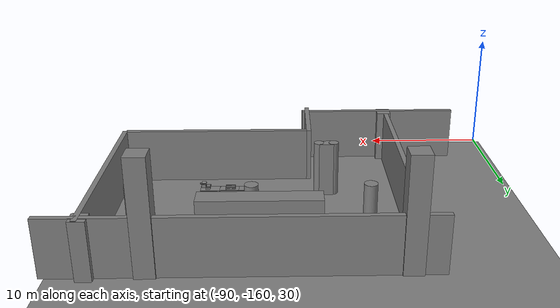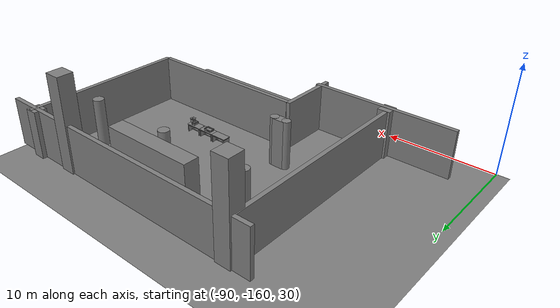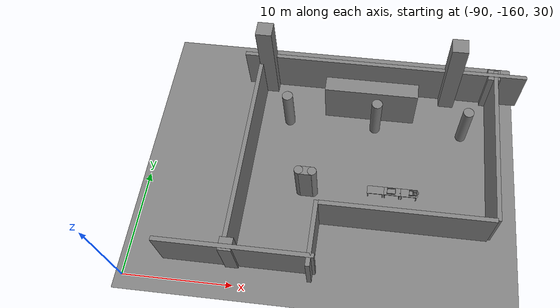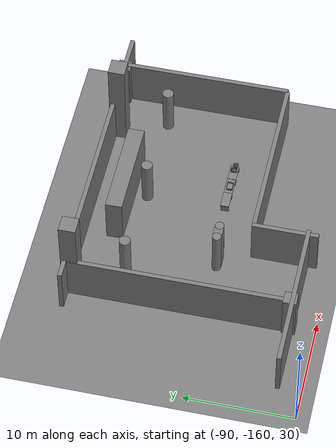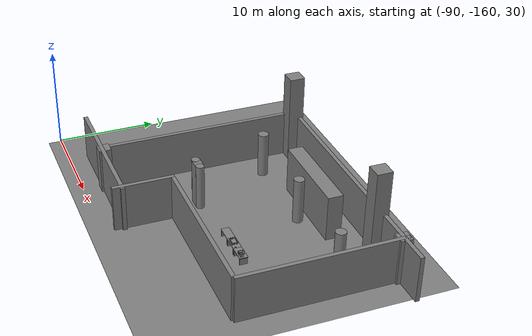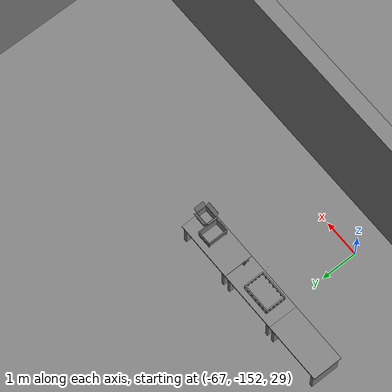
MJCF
<mujoco>
    <option gravity="0.000000000 0.000000000 -9.810000420" timestep="0.0049999999" integrator="implicitfast" density="1.225" viscosity="1.8000001e-05" noslip_iterations="10" iterations="100" sdf_iterations="50">
        <flag multiccd="disable"/>
    </option>
    <size memory="1000M"/>
    <compiler coordinate="local"/>
    <worldbody>
        <light cutoff="30" pos="0 1 1" dir="0 -1 -2"/>
        <light cutoff="30" pos="0 -1 1" dir="0 1 -2"/>
        <body pos="-64.866622925 -149.383972168 30.183746338" euler="89.999992371 89.999946594 0.000000000" name="openloong_gripper_2f85_fix_base_usda_bluebox_01">
            <geom contype="1" conaffinity="1" density="1000" type="box" material="" rgba="0.500000000 0.500000000 0.500000000 1.000000000" solimp="0.899999976 0.949999988 0.001000000" friction="1.000000000 0.005000000 0.000100000" solref="0.020000000 1.000000000" margin="0" condim="3" group="0" pos="0.276596069 0.187225342 0.000061035" quat="0.707107008 0.000077501 0.707106471 0.000077456" size="0.100000001 0.057999998 0.010000000" name="openloong_gripper_2f85_fix_base_usda_geom_7A739D63_E4C9_4440_BA00_556854AA0FDF"/>
            <geom contype="1" conaffinity="1" density="1000" type="box" material="" rgba="0.500000000 0.500000000 0.500000000 1.000000000" solimp="0.899999976 0.949999988 0.001000000" friction="1.000000000 0.005000000 0.000100000" solref="0.020000000 1.000000000" margin="0" condim="3" group="0" pos="0.000000000 0.002883911 0.000000000" quat="1.000000000 0.000000000 0.000000000 0.000000000" size="0.254000008 0.003000000 0.172000006" name="openloong_gripper_2f85_fix_base_usda_geom_E3CA2F68_43D7_45A1_A673_4EF4438BED39"/>
            <geom contype="1" conaffinity="1" density="1000" type="box" material="" rgba="0.500000000 0.500000000 0.500000000 1.000000000" solimp="0.899999976 0.949999988 0.001000000" friction="1.000000000 0.005000000 0.000100000" solref="0.020000000 1.000000000" margin="0" condim="3" group="0" pos="0.000015259 0.124874115 0.173477173" quat="0.999796450 0.020176515 -0.000000015 0.000000030" size="0.259999990 0.119999997 0.007000000" name="openloong_gripper_2f85_fix_base_usda_geom_BE081098_11D6_4D24_9268_4C2609852B4D"/>
            <geom contype="1" conaffinity="1" density="1000" type="box" material="" rgba="0.500000000 0.500000000 0.500000000 1.000000000" solimp="0.899999976 0.949999988 0.001000000" friction="1.000000000 0.005000000 0.000100000" solref="0.020000000 1.000000000" margin="0" condim="3" group="0" pos="0.000015259 0.124874115 -0.173477173" quat="0.999796450 -0.020176545 -0.000000015 0.000000000" size="0.259999990 0.119999997 0.007000000" name="openloong_gripper_2f85_fix_base_usda_geom_A3CB9BD0_12AE_43A3_99C1_F2AA063C291F"/>
            <geom contype="1" conaffinity="1" density="1000" type="box" material="" rgba="0.500000000 0.500000000 0.500000000 1.000000000" solimp="0.899999976 0.949999988 0.001000000" friction="1.000000000 0.005000000 0.000100000" solref="0.020000000 1.000000000" margin="0" condim="3" group="0" pos="0.000015259 0.214012146 0.188980103" quat="0.999913096 0.013176724 0.000000015 0.000000000" size="0.259999990 0.029999999 0.012500000" name="openloong_gripper_2f85_fix_base_usda_geom_D16452AD_419D_49D9_AD57_87090E9EFDA6"/>
            <geom contype="1" conaffinity="1" density="1000" type="box" material="" rgba="0.500000000 0.500000000 0.500000000 1.000000000" solimp="0.899999976 0.949999988 0.001000000" friction="1.000000000 0.005000000 0.000100000" solref="0.020000000 1.000000000" margin="0" condim="3" group="0" pos="-0.258346558 0.125289917 0.001876831" quat="0.702796996 -0.020792052 0.710783184 0.020769238" size="0.189999998 0.119999997 0.009000000" name="openloong_gripper_2f85_fix_base_usda_geom_2A6736DC_3A9A_47D9_A195_1F2BF9471B42"/>
            <geom contype="1" conaffinity="1" density="1000" type="box" material="" rgba="0.500000000 0.500000000 0.500000000 1.000000000" solimp="0.899999976 0.949999988 0.001000000" friction="1.000000000 0.005000000 0.000100000" solref="0.020000000 1.000000000" margin="0" condim="3" group="0" pos="0.000015259 0.214012146 -0.188980103" quat="0.999913096 -0.013176769 0.000000030 0.000000015" size="0.259999990 0.029999999 0.012500000" name="openloong_gripper_2f85_fix_base_usda_geom_352F2D35_8EBB_46F9_89E9_A891D518CB23"/>
            <geom contype="1" conaffinity="1" density="1000" type="box" material="" rgba="0.500000000 0.500000000 0.500000000 1.000000000" solimp="0.899999976 0.949999988 0.001000000" friction="1.000000000 0.005000000 0.000100000" solref="0.020000000 1.000000000" margin="0" condim="3" group="0" pos="-0.276596069 0.187225342 0.000061035" quat="0.707106650 0.000077441 0.707106709 0.000077456" size="0.100000001 0.057999998 0.010000000" name="openloong_gripper_2f85_fix_base_usda_geom_72187FF4_D84C_4595_8DC5_1B5B84A5EA2E"/>
            <geom contype="1" conaffinity="1" density="1000" type="box" material="" rgba="0.500000000 0.500000000 0.500000000 1.000000000" solimp="0.899999976 0.949999988 0.001000000" friction="1.000000000 0.005000000 0.000100000" solref="0.020000000 1.000000000" margin="0" condim="3" group="0" pos="0.258346558 0.125289917 0.001876831" quat="0.702851534 0.018856451 0.710823834 -0.019329429" size="0.189999998 0.119999997 0.009000000" name="openloong_gripper_2f85_fix_base_usda_geom_CA507E66_557A_4C0A_B574_CDB753BE23CC"/>
            <freejoint name="openloong_gripper_2f85_fix_base_usda_bluebox_01_joint"/>
            <site size="0.005000000 0.005000000 0.005000000" rgba="0.500000000 0.500000000 0.500000000 1.000000000" pos="0.000000000 0.000000000 0.000000000" quat="0.999961913 0.008726534 0.000000000 0.000000000" group="0" type="sphere" name="openloong_gripper_2f85_fix_base_usda_bluebox_01site"/>
        </body>
        <body pos="-64.496299744 -149.491867065 30.235729218" euler="0.000000000 0.000000000 89.999946594" name="openloong_gripper_2f85_fix_base_usda_cardboardbox_01">
            <geom contype="1" conaffinity="1" density="1000" type="box" material="" rgba="0.500000000 0.500000000 0.500000000 1.000000000" solimp="0.899999976 0.949999988 0.001000000" friction="1.000000000 0.005000000 0.000100000" solref="0.020000000 1.000000000" margin="0" condim="3" group="0" pos="-0.003166199 -0.004086494 0.005052090" quat="1.000000000 0.000000000 0.000000000 0.000000000" size="0.142499998 0.177500010 0.005000000" name="openloong_gripper_2f85_fix_base_usda_geom_674DCECF_0BCD_4E46_9DEC_E999CDDF9B31"/>
            <geom contype="1" conaffinity="1" density="1000" type="box" material="" rgba="0.500000000 0.500000000 0.500000000 1.000000000" solimp="0.899999976 0.949999988 0.001000000" friction="1.000000000 0.005000000 0.000100000" solref="0.020000000 1.000000000" margin="0" condim="3" group="0" pos="-0.003166199 0.170316696 0.150570869" quat="1.000000000 0.000000000 0.000000000 0.000000000" size="0.142499998 0.005000000 0.149999991" name="openloong_gripper_2f85_fix_base_usda_geom_7C47CF13_2F63_42DD_A772_1F2AF0DF3EF7"/>
            <geom contype="1" conaffinity="1" density="1000" type="box" material="" rgba="0.500000000 0.500000000 0.500000000 1.000000000" solimp="0.899999976 0.949999988 0.001000000" friction="1.000000000 0.005000000 0.000100000" solref="0.020000000 1.000000000" margin="0" condim="3" group="0" pos="-0.147399902 -0.005307198 0.150570869" quat="1.000000000 0.000000000 0.000000000 0.000000000" size="0.005000000 0.177500010 0.149999991" name="openloong_gripper_2f85_fix_base_usda_geom_55190455_C914_4028_A6D9_2F4207CC8BBD"/>
            <geom contype="1" conaffinity="1" density="1000" type="box" material="" rgba="0.500000000 0.500000000 0.500000000 1.000000000" solimp="0.899999976 0.949999988 0.001000000" friction="1.000000000 0.005000000 0.000100000" solref="0.020000000 1.000000000" margin="0" condim="3" group="0" pos="0.140275955 -0.005307198 0.150570869" quat="1.000000000 0.000000000 0.000000000 0.000000000" size="0.005000000 0.177500010 0.149999991" name="openloong_gripper_2f85_fix_base_usda_geom_FCBB40B7_2519_4D1A_853C_2608F7F8C850"/>
            <geom contype="1" conaffinity="1" density="1000" type="box" material="" rgba="0.500000000 0.500000000 0.500000000 1.000000000" solimp="0.899999976 0.949999988 0.001000000" friction="1.000000000 0.005000000 0.000100000" solref="0.020000000 1.000000000" margin="0" condim="3" group="0" pos="-0.003166199 -0.181550980 0.150570869" quat="1.000000000 0.000000000 0.000000000 0.000000000" size="0.142499998 0.005000000 0.149999991" name="openloong_gripper_2f85_fix_base_usda_geom_1AD6218D_91EF_4500_A4E3_9AB762E754EC"/>
            <freejoint name="openloong_gripper_2f85_fix_base_usda_cardboardbox_01_joint"/>
            <site size="0.005000000 0.005000000 0.005000000" rgba="0.500000000 0.500000000 0.500000000 1.000000000" pos="0.000000000 0.000000000 0.000000000" quat="0.999961913 0.008726535 0.000000000 0.000000000" group="0" type="sphere" name="openloong_gripper_2f85_fix_base_usda_site_4C84F935_3B9E_459D_9364_0FF048A58A35"/>
            <body pos="0.139160156 -0.004048347 0.301930904" euler="-179.999954224 49.383502960 179.999954224" name="openloong_gripper_2f85_fix_base_usda_A1_006">
                <geom contype="1" conaffinity="1" density="1000" type="box" material="" rgba="0.500000000 0.500000000 0.500000000 1.000000000" solimp="0.899999976 0.949999988 0.001000000" friction="1.000000000 0.005000000 0.000100000" solref="0.020000000 1.000000000" margin="0" condim="3" group="0" pos="-0.071587563 0.000009537 0.001745224" quat="0.999999881 0.000000000 0.000000000 0.000000000" size="0.071249999 0.179999992 0.002500000" name="openloong_gripper_2f85_fix_base_usda_geom_275C665C_1BFB_4B2B_862B_946867E7B844"/>
                <joint armature="0" stiffness="0.07" damping="0.0099999998" axis="0.000000 1.000000 0.000000" type="hinge" name="openloong_gripper_2f85_fix_base_usda_A1_006"/>
            </body>
            <body pos="-0.145902634 -0.004086494 0.301938057" euler="-180.000000000 -60.000011444 -180.000000000" name="openloong_gripper_2f85_fix_base_usda_A2_006">
                <geom contype="1" conaffinity="1" density="1000" type="box" material="" rgba="0.500000000 0.500000000 0.500000000 1.000000000" solimp="0.899999976 0.949999988 0.001000000" friction="1.000000000 0.005000000 0.000100000" solref="0.020000000 1.000000000" margin="0" condim="3" group="0" pos="0.071268082 0.000009537 0.002717972" quat="0.000002921 0.000000000 -0.000000030 0.999999881" size="0.071249999 0.179999992 0.002500000" name="openloong_gripper_2f85_fix_base_usda_geom_F498F1D9_317F_4E73_AFBE_158541D6B115"/>
                <joint armature="0" stiffness="0.07" damping="0.0099999998" axis="0.000000 1.000000 0.000000" type="hinge" name="openloong_gripper_2f85_fix_base_usda_A2_006"/>
            </body>
            <body pos="-0.003385544 0.175991058 0.301930904" euler="-125.858116150 -0.000004561 0.000002331" name="openloong_gripper_2f85_fix_base_usda_B2_006">
                <geom contype="1" conaffinity="1" density="1000" type="box" material="" rgba="0.500000000 0.500000000 0.500000000 1.000000000" solimp="0.899999976 0.949999988 0.001000000" friction="1.000000000 0.005000000 0.000100000" solref="0.020000000 1.000000000" margin="0" condim="3" group="0" pos="0.000009537 -0.070939064 -0.002470016" quat="0.999614120 0.027776197 -0.000000015 0.000000030" size="0.137500003 0.064999998 0.005000000" name="openloong_gripper_2f85_fix_base_usda_geom_4B46C37B_FEA5_4F4C_9047_E7D479E8409C"/>
                <joint armature="0" stiffness="0.07" damping="0.0099999998" axis="1.000000 0.000000 0.000000" type="hinge" name="openloong_gripper_2f85_fix_base_usda_B2_006"/>
            </body>
            <body pos="-0.003385544 -0.184140205 0.301938057" euler="147.805557251 0.000000000 0.000000000" name="openloong_gripper_2f85_fix_base_usda_B1_006">
                <geom contype="1" conaffinity="1" density="1000" type="box" material="" rgba="0.500000000 0.500000000 0.500000000 1.000000000" solimp="0.899999976 0.949999988 0.001000000" friction="1.000000000 0.005000000 0.000100000" solref="0.020000000 1.000000000" margin="0" condim="3" group="0" pos="-0.000028610 0.070202351 -0.002703667" quat="0.999614179 -0.027776167 0.000000000 0.000000000" size="0.137500003 0.064999998 0.005000000" name="openloong_gripper_2f85_fix_base_usda_geom_4C8D50BD_C75A_40C0_A785_8D5A0336956F"/>
                <joint armature="0" stiffness="0.07" damping="0.0099999998" axis="1.000000 0.000000 0.000000" type="hinge" name="openloong_gripper_2f85_fix_base_usda_B1_006"/>
            </body>
        </body>
        <body pos="-65.882858276 -149.481979370 30.229999542" euler="-64.487716675 0.000000000 0.000000000" name="openloong_gripper_2f85_fix_base_usda_Barcode">
            <geom contype="1" conaffinity="1" density="1000" type="box" material="" rgba="0.500000000 0.500000000 0.500000000 1.000000000" solimp="0.899999976 0.949999988 0.001000000" friction="1.000000000 0.005000000 0.000100000" solref="0.020000000 1.000000000" margin="0" condim="3" group="0" pos="0.000000000 0.013038635 0.001419067" quat="0.000000000 0.000000000 0.000000000 1.000000119" size="0.034000002 0.010000000 0.017999999" name="openloong_gripper_2f85_fix_base_usda_geom_303F2A17_2033_4457_B0ED_2DA3C2558764"/>
            <geom contype="1" conaffinity="1" density="1000" type="box" material="" rgba="0.500000000 0.500000000 0.500000000 1.000000000" solimp="0.899999976 0.949999988 0.001000000" friction="1.000000000 0.005000000 0.000100000" solref="0.020000000 1.000000000" margin="0" condim="3" group="0" pos="0.000000000 -0.035301208 -0.007095337" quat="0.000000000 0.000000000 -0.043619365 0.999048233" size="0.028999999 0.010000000 0.020000000" name="openloong_gripper_2f85_fix_base_usda_geom_B773759C_2038_4F6F_9207_B59EE56F9B70"/>
            <geom contype="1" conaffinity="1" density="1000" type="box" material="" rgba="0.500000000 0.500000000 0.500000000 1.000000000" solimp="0.899999976 0.949999988 0.001000000" friction="1.000000000 0.005000000 0.000100000" solref="0.020000000 1.000000000" margin="0" condim="3" group="0" pos="0.000000000 -0.043411255 -0.011749268" quat="0.922262907 0.386563420 0.000000000 0.000000000" size="0.026000001 0.010000000 0.020000000" name="openloong_gripper_2f85_fix_base_usda_geom_4445CB8B_8B89_4991_B431_A602F6B7907A"/>
            <geom contype="1" conaffinity="1" density="1000" type="box" material="" rgba="0.500000000 0.500000000 0.500000000 1.000000000" solimp="0.899999976 0.949999988 0.001000000" friction="1.000000000 0.005000000 0.000100000" solref="0.020000000 1.000000000" margin="0" condim="3" group="0" pos="0.000000000 -0.016967773 -0.031860352" quat="0.000000000 0.000000000 0.000000000 1.000000119" size="0.008000000 0.010000000 0.013000000" name="openloong_gripper_2f85_fix_base_usda_geom_B2A013F3_F7AD_4040_9696_A7B9EAF4524E"/>
            <geom contype="1" conaffinity="1" density="1000" type="box" material="" rgba="0.500000000 0.500000000 0.500000000 1.000000000" solimp="0.899999976 0.949999988 0.001000000" friction="1.000000000 0.005000000 0.000100000" solref="0.020000000 1.000000000" margin="0" condim="3" group="0" pos="0.000000000 -0.001869202 0.000312805" quat="0.953716993 0.300705761 0.000000000 0.000000000" size="0.032000002 0.010000000 0.018999999" name="openloong_gripper_2f85_fix_base_usda_geom_F1F8647B_CB3B_4EBD_9E2F_8228615C4C98"/>
            <geom contype="1" conaffinity="1" density="1000" type="box" material="" rgba="0.500000000 0.500000000 0.500000000 1.000000000" solimp="0.899999976 0.949999988 0.001000000" friction="1.000000000 0.005000000 0.000100000" solref="0.020000000 1.000000000" margin="0" condim="3" group="0" pos="0.000000000 -0.019531250 -0.003173828" quat="0.953716993 0.300705761 0.000000000 0.000000000" size="0.030999999 0.010000000 0.020000000" name="openloong_gripper_2f85_fix_base_usda_geom_199473E3_A4A8_466D_8876_14FC65E26CED"/>
            <geom contype="1" conaffinity="1" density="1000" type="box" material="" rgba="0.500000000 0.500000000 0.500000000 1.000000000" solimp="0.899999976 0.949999988 0.001000000" friction="1.000000000 0.005000000 0.000100000" solref="0.020000000 1.000000000" margin="0" condim="3" group="0" pos="0.000000000 -0.035301208 -0.007095337" quat="0.953716993 0.300705761 0.000000000 0.000000000" size="0.028999999 0.010000000 0.020000000" name="openloong_gripper_2f85_fix_base_usda_geom_30AFB2B4_4948_4FE2_BFD8_1A369A7A5686"/>
            <geom contype="1" conaffinity="1" density="1000" type="box" material="" rgba="0.500000000 0.500000000 0.500000000 1.000000000" solimp="0.899999976 0.949999988 0.001000000" friction="1.000000000 0.005000000 0.000100000" solref="0.020000000 1.000000000" margin="0" condim="3" group="0" pos="0.000000000 -0.042617798 -0.071121216" quat="0.000000000 0.000000000 0.000000000 1.000000119" size="0.013000000 0.021000000 0.059999999" name="openloong_gripper_2f85_fix_base_usda_geom_DD2A2F71_E7E2_44BF_A188_14A2323B25AD"/>
            <freejoint name="openloong_gripper_2f85_fix_base_usda_Barcode_joint"/>
            <site size="0.005000000 0.005000000 0.005000000" rgba="0.500000000 0.500000000 0.500000000 1.000000000" pos="0.000000000 0.000000000 0.000000000" quat="1.000000000 0.000000000 0.000000000 0.000000000" group="0" type="sphere" name="openloong_gripper_2f85_fix_base_usda_Barcode_site"/>
        </body>
        <body pos="-66.745018005 -149.392349243 30.184000015" euler="0.000000000 0.000000000 89.999946594" name="[22332242754445]_Basket_01">
            <geom contype="1" conaffinity="1" density="1000" type="box" material="" rgba="0.500000000 0.500000000 0.500000000 1.000000000" solimp="0.899999976 0.949999988 0.001000000" friction="1.000000000 0.005000000 0.000100000" solref="0.020000000 1.000000000" margin="0" condim="3" group="0" pos="-0.052425385 0.389207840 0.089787483" quat="0.707107008 0.000000000 0.000000000 0.707106411" size="0.014249999 0.014249999 0.059999999" name="[22332242754445]_geom_38EABD5D_D525_4A03_B046_09C32C41C9FD"/>
            <geom contype="1" conaffinity="1" density="1000" type="box" material="" rgba="0.500000000 0.500000000 0.500000000 1.000000000" solimp="0.899999976 0.949999988 0.001000000" friction="1.000000000 0.005000000 0.000100000" solref="0.020000000 1.000000000" margin="0" condim="3" group="0" pos="0.264015198 -0.133043289 0.089787483" quat="0.707107008 0.000000000 0.000000000 0.707106411" size="0.014249999 0.014249999 0.059999999" name="[22332242754445]_geom_28EC34BB_7C2D_407A_886C_B68AF32BDF6B"/>
            <geom contype="1" conaffinity="1" density="1000" type="box" material="" rgba="0.500000000 0.500000000 0.500000000 1.000000000" solimp="0.899999976 0.949999988 0.001000000" friction="1.000000000 0.005000000 0.000100000" solref="0.020000000 1.000000000" margin="0" condim="3" group="0" pos="-0.264015198 -0.265548706 0.089793205" quat="0.707107008 0.000000000 0.000000000 0.707106411" size="0.014249999 0.014249999 0.059999999" name="[22332242754445]_geom_4097BEFE_AE2F_42B4_9135_517CDB1217B5"/>
            <geom contype="1" conaffinity="1" density="1000" type="box" material="" rgba="0.500000000 0.500000000 0.500000000 1.000000000" solimp="0.899999976 0.949999988 0.001000000" friction="1.000000000 0.005000000 0.000100000" solref="0.020000000 1.000000000" margin="0" condim="3" group="0" pos="-0.160263062 -0.389322281 0.089793205" quat="0.707107008 0.000000000 0.000000000 0.707106411" size="0.014249999 0.014249999 0.059999999" name="[22332242754445]_geom_38149C14_9DE0_4475_AB04_012518F839E5"/>
            <geom contype="1" conaffinity="1" density="1000" type="box" material="" rgba="0.500000000 0.500000000 0.500000000 1.000000000" solimp="0.899999976 0.949999988 0.001000000" friction="1.000000000 0.005000000 0.000100000" solref="0.020000000 1.000000000" margin="0" condim="3" group="0" pos="0.162265778 -0.389322281 0.089787483" quat="0.707107008 0.000000000 0.000000000 0.707106411" size="0.014249999 0.014249999 0.059999999" name="[22332242754445]_geom_C60AFC9C_C779_4698_8E2A_FF06988647D2"/>
            <geom contype="1" conaffinity="1" density="1000" type="box" material="" rgba="0.500000000 0.500000000 0.500000000 1.000000000" solimp="0.899999976 0.949999988 0.001000000" friction="1.000000000 0.005000000 0.000100000" solref="0.020000000 1.000000000" margin="0" condim="3" group="0" pos="0.264015198 0.389207840 0.089787483" quat="0.707107008 0.000000000 0.000000000 0.707106411" size="0.014249999 0.014249999 0.059999999" name="[22332242754445]_geom_A172A1EF_6387_4139_B560_E0E6D60DF341"/>
            <geom contype="1" conaffinity="1" density="1000" type="box" material="" rgba="0.500000000 0.500000000 0.500000000 1.000000000" solimp="0.899999976 0.949999988 0.001000000" friction="1.000000000 0.005000000 0.000100000" solref="0.020000000 1.000000000" margin="0" condim="3" group="0" pos="-0.264015198 -0.133043289 0.089793205" quat="0.707107008 0.000000000 0.000000000 0.707106411" size="0.014249999 0.014249999 0.059999999" name="[22332242754445]_geom_3F1F2149_4D53_45FB_AB40_0CC6A787BB9B"/>
            <geom contype="1" conaffinity="1" density="1000" type="box" material="" rgba="0.500000000 0.500000000 0.500000000 1.000000000" solimp="0.899999976 0.949999988 0.001000000" friction="1.000000000 0.005000000 0.000100000" solref="0.020000000 1.000000000" margin="0" condim="3" group="0" pos="-0.264026642 0.269256592 0.089793205" quat="0.707107008 0.000000000 0.000000000 0.707106411" size="0.014249999 0.014249999 0.059999999" name="[22332242754445]_geom_85B0E178_F306_42ED_9D85_B540E8E386FF"/>
            <geom contype="1" conaffinity="1" density="1000" type="box" material="" rgba="0.500000000 0.500000000 0.500000000 1.000000000" solimp="0.899999976 0.949999988 0.001000000" friction="1.000000000 0.005000000 0.000100000" solref="0.020000000 1.000000000" margin="0" condim="3" group="0" pos="0.054462433 0.389207840 0.089787483" quat="0.707107008 0.000000000 0.000000000 0.707106411" size="0.014249999 0.014249999 0.059999999" name="[22332242754445]_geom_0A642672_E96D_4E80_B528_BE4F78D90E27"/>
            <geom contype="1" conaffinity="1" density="1000" type="box" material="" rgba="0.500000000 0.500000000 0.500000000 1.000000000" solimp="0.899999976 0.949999988 0.001000000" friction="1.000000000 0.005000000 0.000100000" solref="0.020000000 1.000000000" margin="0" condim="3" group="0" pos="0.054462433 -0.389322281 0.089787483" quat="0.707107008 0.000000000 0.000000000 0.707106411" size="0.014249999 0.014249999 0.059999999" name="[22332242754445]_geom_7F3F9A46_0B6D_4E8F_8523_93B43980C8CB"/>
            <geom contype="1" conaffinity="1" density="1000" type="box" material="" rgba="0.500000000 0.500000000 0.500000000 1.000000000" solimp="0.899999976 0.949999988 0.001000000" friction="1.000000000 0.005000000 0.000100000" solref="0.020000000 1.000000000" margin="0" condim="3" group="0" pos="0.264015198 0.269256592 0.089793205" quat="0.707107008 0.000000000 0.000000000 0.707106411" size="0.014249999 0.014249999 0.059999999" name="[22332242754445]_geom_84949A33_E194_4570_A153_DD0F73EFBD96"/>
            <geom contype="1" conaffinity="1" density="1000" type="box" material="" rgba="0.500000000 0.500000000 0.500000000 1.000000000" solimp="0.899999976 0.949999988 0.001000000" friction="1.000000000 0.005000000 0.000100000" solref="0.020000000 1.000000000" margin="0" condim="3" group="0" pos="0.264015198 -0.389322281 0.089787483" quat="0.707107008 0.000000000 0.000000000 0.707106411" size="0.014249999 0.014249999 0.059999999" name="[22332242754445]_geom_1EBE0624_DBA7_4735_8D21_5141F3A5D31F"/>
            <geom contype="1" conaffinity="1" density="1000" type="box" material="" rgba="0.500000000 0.500000000 0.500000000 1.000000000" solimp="0.899999976 0.949999988 0.001000000" friction="1.000000000 0.005000000 0.000100000" solref="0.020000000 1.000000000" margin="0" condim="3" group="0" pos="0.000000000 0.000000000 0.015998840" quat="0.707107008 0.000000000 0.000000000 0.707106411" size="0.403499991 0.279000014 0.015750000" name="[22332242754445]_geom_BAB0B5C5_AC8E_4CED_91C0_03C257FEC430"/>
            <geom contype="1" conaffinity="1" density="1000" type="box" material="" rgba="0.500000000 0.500000000 0.500000000 1.000000000" solimp="0.899999976 0.949999988 0.001000000" friction="1.000000000 0.005000000 0.000100000" solref="0.020000000 1.000000000" margin="0" condim="3" group="0" pos="0.000000000 -0.389476776 0.163619041" quat="0.707107008 0.000000000 0.000000000 0.707106411" size="0.015000000 0.277500004 0.015750000" name="[22332242754445]_geom_9099FDBB_41C9_419C_A580_4B1D28C87B1F"/>
            <geom contype="1" conaffinity="1" density="1000" type="box" material="" rgba="0.500000000 0.500000000 0.500000000 1.000000000" solimp="0.899999976 0.949999988 0.001000000" friction="1.000000000 0.005000000 0.000100000" solref="0.020000000 1.000000000" margin="0" condim="3" group="0" pos="0.162265778 0.389207840 0.089787483" quat="0.707107008 0.000000000 0.000000000 0.707106411" size="0.014249999 0.014249999 0.059999999" name="[22332242754445]_geom_C8B066AD_86EC_491C_9688_96D3A8B44334"/>
            <geom contype="1" conaffinity="1" density="1000" type="box" material="" rgba="0.500000000 0.500000000 0.500000000 1.000000000" solimp="0.899999976 0.949999988 0.001000000" friction="1.000000000 0.005000000 0.000100000" solref="0.020000000 1.000000000" margin="0" condim="3" group="0" pos="0.000000000 0.389471054 0.163619041" quat="0.707107008 0.000000000 0.000000000 0.707106411" size="0.015000000 0.277500004 0.015750000" name="[22332242754445]_geom_72D23F09_AA99_47A9_9EE8_2C22B6339B8C"/>
            <geom contype="1" conaffinity="1" density="1000" type="box" material="" rgba="0.500000000 0.500000000 0.500000000 1.000000000" solimp="0.899999976 0.949999988 0.001000000" friction="1.000000000 0.005000000 0.000100000" solref="0.020000000 1.000000000" margin="0" condim="3" group="0" pos="-0.263511658 0.000000000 0.163619041" quat="0.707107008 0.000000000 0.000000000 0.707106411" size="0.403499991 0.015000000 0.015750000" name="[22332242754445]_geom_14FAA39A_8BD3_4661_A37A_4555E25EE7E5"/>
            <geom contype="1" conaffinity="1" density="1000" type="box" material="" rgba="0.500000000 0.500000000 0.500000000 1.000000000" solimp="0.899999976 0.949999988 0.001000000" friction="1.000000000 0.005000000 0.000100000" solref="0.020000000 1.000000000" margin="0" condim="3" group="0" pos="-0.264015198 0.141334534 0.089793205" quat="0.707107008 0.000000000 0.000000000 0.707106411" size="0.014249999 0.014249999 0.059999999" name="[22332242754445]_geom_5D0774C3_02AE_40F5_99C6_9B8D77E19D5B"/>
            <geom contype="1" conaffinity="1" density="1000" type="box" material="" rgba="0.500000000 0.500000000 0.500000000 1.000000000" solimp="0.899999976 0.949999988 0.001000000" friction="1.000000000 0.005000000 0.000100000" solref="0.020000000 1.000000000" margin="0" condim="3" group="0" pos="0.264015198 -0.265548706 0.089787483" quat="0.707107008 0.000000000 0.000000000 0.707106411" size="0.014249999 0.014249999 0.059999999" name="[22332242754445]_geom_4AF9DD22_DBF3_443B_A43D_72722F21C1F6"/>
            <geom contype="1" conaffinity="1" density="1000" type="box" material="" rgba="0.500000000 0.500000000 0.500000000 1.000000000" solimp="0.899999976 0.949999988 0.001000000" friction="1.000000000 0.005000000 0.000100000" solref="0.020000000 1.000000000" margin="0" condim="3" group="0" pos="-0.160263062 0.389207840 0.089787483" quat="0.707107008 0.000000000 0.000000000 0.707106411" size="0.014249999 0.014249999 0.059999999" name="[22332242754445]_geom_A8A2DE5A_EE7E_4F7A_A31F_C81B2C54A820"/>
            <geom contype="1" conaffinity="1" density="1000" type="box" material="" rgba="0.500000000 0.500000000 0.500000000 1.000000000" solimp="0.899999976 0.949999988 0.001000000" friction="1.000000000 0.005000000 0.000100000" solref="0.020000000 1.000000000" margin="0" condim="3" group="0" pos="-0.052425385 -0.389322281 0.089787483" quat="0.707107008 0.000000000 0.000000000 0.707106411" size="0.014249999 0.014249999 0.059999999" name="[22332242754445]_geom_18DE5F6A_AEEB_4573_B337_5133D5FFBAA2"/>
            <geom contype="1" conaffinity="1" density="1000" type="box" material="" rgba="0.500000000 0.500000000 0.500000000 1.000000000" solimp="0.899999976 0.949999988 0.001000000" friction="1.000000000 0.005000000 0.000100000" solref="0.020000000 1.000000000" margin="0" condim="3" group="0" pos="-0.264026642 -0.389322281 0.089793205" quat="0.707107008 0.000000000 0.000000000 0.707106411" size="0.014249999 0.014249999 0.059999999" name="[22332242754445]_geom_8CDE5272_4360_41F0_AD94_D25C2558E9ED"/>
            <geom contype="1" conaffinity="1" density="1000" type="box" material="" rgba="0.500000000 0.500000000 0.500000000 1.000000000" solimp="0.899999976 0.949999988 0.001000000" friction="1.000000000 0.005000000 0.000100000" solref="0.020000000 1.000000000" margin="0" condim="3" group="0" pos="0.264015198 0.141334534 0.089787483" quat="0.707107008 0.000000000 0.000000000 0.707106411" size="0.014249999 0.014249999 0.059999999" name="[22332242754445]_geom_ECB8C277_D32E_48D8_A119_4C83CF608868"/>
            <geom contype="1" conaffinity="1" density="1000" type="box" material="" rgba="0.500000000 0.500000000 0.500000000 1.000000000" solimp="0.899999976 0.949999988 0.001000000" friction="1.000000000 0.005000000 0.000100000" solref="0.020000000 1.000000000" margin="0" condim="3" group="0" pos="-0.264015198 0.389207840 0.089793205" quat="0.707107008 0.000000000 0.000000000 0.707106411" size="0.014249999 0.014249999 0.059999999" name="[22332242754445]_geom_4992DBA7_149D_4E6C_9A6B_A93F8642FAC6"/>
            <geom contype="1" conaffinity="1" density="1000" type="box" material="" rgba="0.500000000 0.500000000 0.500000000 1.000000000" solimp="0.899999976 0.949999988 0.001000000" friction="1.000000000 0.005000000 0.000100000" solref="0.020000000 1.000000000" margin="0" condim="3" group="0" pos="0.264015198 0.004480362 0.089787483" quat="0.707107008 0.000000000 0.000000000 0.707106411" size="0.014249999 0.014249999 0.059999999" name="[22332242754445]_geom_0F7764AB_C554_4ED8_99DB_8B3C38021688"/>
            <geom contype="1" conaffinity="1" density="1000" type="box" material="" rgba="0.500000000 0.500000000 0.500000000 1.000000000" solimp="0.899999976 0.949999988 0.001000000" friction="1.000000000 0.005000000 0.000100000" solref="0.020000000 1.000000000" margin="0" condim="3" group="0" pos="0.263694763 -0.000011444 0.163619041" quat="0.707107008 0.000000000 0.000000000 0.707106411" size="0.403499991 0.015000000 0.015750000" name="[22332242754445]_geom_3B67F043_2E4E_452F_A3C1_E3E9D8ABC926"/>
            <geom contype="1" conaffinity="1" density="1000" type="box" material="" rgba="0.500000000 0.500000000 0.500000000 1.000000000" solimp="0.899999976 0.949999988 0.001000000" friction="1.000000000 0.005000000 0.000100000" solref="0.020000000 1.000000000" margin="0" condim="3" group="0" pos="-0.264015198 0.004480362 0.089793205" quat="0.707107008 0.000000000 0.000000000 0.707106411" size="0.014249999 0.014249999 0.059999999" name="[22332242754445]_geom_36E85105_6484_4353_9EEE_F48F37F4BBB5"/>
            <freejoint name="[22332242754445]_joint_6164DD14_B485_4ADB_A194_CBB71249CF08"/>
        </body>
        <body pos="0.000000000 0.000000000 0.000000000" euler="0.000000000 0.000000000 0.000000000" name="Static Objects_Static Objects">
            <geom contype="1" conaffinity="1" density="1000" type="box" material="" rgba="0.500000000 0.500000000 0.500000000 1.000000000" solimp="0.899999976 0.949999988 0.001000000" friction="1.000000000 0.005000000 0.000100000" solref="0.020000000 1.000000000" margin="0" condim="3" group="0" pos="-67.544113159 -149.365814209 29.727830887" quat="0.500000417 0.499999970 0.499999553 0.499999970" size="0.381000012 0.319999993 0.041000001" name="Static Objects_geom_46270E82_123C_4E45_A9B5_6843BAD6E451"/>
            <geom contype="1" conaffinity="1" density="1000" type="box" material="" rgba="0.500000000 0.500000000 0.500000000 1.000000000" solimp="0.899999976 0.949999988 0.001000000" friction="1.000000000 0.005000000 0.000100000" solref="0.020000000 1.000000000" margin="0" condim="3" group="0" pos="-68.239501953 -149.365814209 30.086868286" quat="0.500000417 0.499999970 0.499999553 0.499999970" size="0.370999992 0.039500002 0.745000005" name="Static Objects_geom_1BB508AB_4FBE_48E0_AF95_A6AA77F53788"/>
            <geom contype="1" conaffinity="1" density="1000" type="box" material="" rgba="0.500000000 0.500000000 0.500000000 1.000000000" solimp="0.899999976 0.949999988 0.001000000" friction="1.000000000 0.005000000 0.000100000" solref="0.020000000 1.000000000" margin="0" condim="3" group="0" pos="-68.239501953 -149.365814209 30.147235870" quat="0.500000417 0.499999970 0.499999553 0.499999970" size="0.400000006 0.022000000 0.800000012" name="Static Objects_geom_1D8D39DE_F913_40D2_9A4F_23E588E01593"/>
            <geom contype="1" conaffinity="1" density="1000" type="box" material="" rgba="0.500000000 0.500000000 0.500000000 1.000000000" solimp="0.899999976 0.949999988 0.001000000" friction="1.000000000 0.005000000 0.000100000" solref="0.020000000 1.000000000" margin="0" condim="3" group="0" pos="-68.934890747 -149.365814209 29.727830887" quat="0.500000417 0.499999970 0.499999553 0.499999970" size="0.381000012 0.319999993 0.041000001" name="Static Objects_geom_53966871_84BC_403D_BAE6_064F6556CFE8"/>
            <geom contype="1" conaffinity="1" density="1000" type="box" material="" rgba="0.500000000 0.500000000 0.500000000 1.000000000" solimp="0.899999976 0.949999988 0.001000000" friction="1.000000000 0.005000000 0.000100000" solref="0.020000000 1.000000000" margin="0" condim="3" group="0" pos="-68.239501953 -149.365814209 29.561563492" quat="0.500000417 0.499999970 0.499999553 0.499999970" size="0.020000000 0.022000000 0.660000026" name="Static Objects_geom_68432A1C_1350_4788_AD74_0C63FABE75DE"/>
            <geom contype="1" conaffinity="1" density="1000" type="box" material="" rgba="0.500000000 0.500000000 0.500000000 1.000000000" solimp="0.899999976 0.949999988 0.001000000" friction="1.000000000 0.005000000 0.000100000" solref="0.020000000 1.000000000" margin="0" condim="3" group="0" pos="-65.945671082 -149.365814209 29.727830887" quat="0.500000417 0.499999970 0.499999553 0.499999970" size="0.381000012 0.319999993 0.041000001" name="Static Objects_geom_1A4D6DA4_0125_49AC_A5D2_F70FF16C119C"/>
            <geom contype="1" conaffinity="1" density="1000" type="box" material="" rgba="0.500000000 0.500000000 0.500000000 1.000000000" solimp="0.899999976 0.949999988 0.001000000" friction="1.000000000 0.005000000 0.000100000" solref="0.020000000 1.000000000" margin="0" condim="3" group="0" pos="-66.641059875 -149.365814209 30.086868286" quat="0.500000417 0.499999970 0.499999553 0.499999970" size="0.370999992 0.039500002 0.745000005" name="Static Objects_geom_F9D767FF_6A4A_4923_853C_BAFF490EB066"/>
            <geom contype="1" conaffinity="1" density="1000" type="box" material="" rgba="0.500000000 0.500000000 0.500000000 1.000000000" solimp="0.899999976 0.949999988 0.001000000" friction="1.000000000 0.005000000 0.000100000" solref="0.020000000 1.000000000" margin="0" condim="3" group="0" pos="-66.641059875 -149.365814209 30.147235870" quat="0.500000417 0.499999970 0.499999553 0.499999970" size="0.400000006 0.022000000 0.800000012" name="Static Objects_geom_34693BE5_01D9_4094_890C_D4A5134137ED"/>
            <geom contype="1" conaffinity="1" density="1000" type="box" material="" rgba="0.500000000 0.500000000 0.500000000 1.000000000" solimp="0.899999976 0.949999988 0.001000000" friction="1.000000000 0.005000000 0.000100000" solref="0.020000000 1.000000000" margin="0" condim="3" group="0" pos="-67.336448669 -149.365814209 29.727830887" quat="0.500000417 0.499999970 0.499999553 0.499999970" size="0.381000012 0.319999993 0.041000001" name="Static Objects_geom_8AE3CC24_4095_4D50_A4E5_858ACB050762"/>
            <geom contype="1" conaffinity="1" density="1000" type="box" material="" rgba="0.500000000 0.500000000 0.500000000 1.000000000" solimp="0.899999976 0.949999988 0.001000000" friction="1.000000000 0.005000000 0.000100000" solref="0.020000000 1.000000000" margin="0" condim="3" group="0" pos="-66.641059875 -149.365814209 29.561563492" quat="0.500000417 0.499999970 0.499999553 0.499999970" size="0.020000000 0.022000000 0.660000026" name="Static Objects_geom_DBC85D75_AD75_4475_906F_826CF12F311C"/>
            <geom contype="1" conaffinity="1" density="1000" type="box" material="" rgba="0.500000000 0.500000000 0.500000000 1.000000000" solimp="0.899999976 0.949999988 0.001000000" friction="1.000000000 0.005000000 0.000100000" solref="0.020000000 1.000000000" margin="0" condim="3" group="0" pos="-64.338577271 -149.365814209 29.727830887" quat="0.500000417 0.499999970 0.499999553 0.499999970" size="0.381000012 0.319999993 0.041000001" name="Static Objects_geom_939BD28B_7AB9_4666_8E7A_92260EA8D2EC"/>
            <geom contype="1" conaffinity="1" density="1000" type="box" material="" rgba="0.500000000 0.500000000 0.500000000 1.000000000" solimp="0.899999976 0.949999988 0.001000000" friction="1.000000000 0.005000000 0.000100000" solref="0.020000000 1.000000000" margin="0" condim="3" group="0" pos="-65.033966064 -149.365814209 30.086868286" quat="0.500000417 0.499999970 0.499999553 0.499999970" size="0.370999992 0.039500002 0.745000005" name="Static Objects_geom_43832935_2217_4BED_BB3B_7E682EF99A83"/>
            <geom contype="1" conaffinity="1" density="1000" type="box" material="" rgba="0.500000000 0.500000000 0.500000000 1.000000000" solimp="0.899999976 0.949999988 0.001000000" friction="1.000000000 0.005000000 0.000100000" solref="0.020000000 1.000000000" margin="0" condim="3" group="0" pos="-65.033966064 -149.365814209 30.147235870" quat="0.500000417 0.499999970 0.499999553 0.499999970" size="0.400000006 0.022000000 0.800000012" name="Static Objects_geom_C7E6C69B_183A_4873_A1AD_7E1B258BECB4"/>
            <geom contype="1" conaffinity="1" density="1000" type="box" material="" rgba="0.500000000 0.500000000 0.500000000 1.000000000" solimp="0.899999976 0.949999988 0.001000000" friction="1.000000000 0.005000000 0.000100000" solref="0.020000000 1.000000000" margin="0" condim="3" group="0" pos="-65.729354858 -149.365814209 29.727830887" quat="0.500000417 0.499999970 0.499999553 0.499999970" size="0.381000012 0.319999993 0.041000001" name="Static Objects_geom_BAF54355_CD2D_4DE7_B088_5D7B613F3AB6"/>
            <geom contype="1" conaffinity="1" density="1000" type="box" material="" rgba="0.500000000 0.500000000 0.500000000 1.000000000" solimp="0.899999976 0.949999988 0.001000000" friction="1.000000000 0.005000000 0.000100000" solref="0.020000000 1.000000000" margin="0" condim="3" group="0" pos="-65.033966064 -149.365814209 29.561563492" quat="0.500000417 0.499999970 0.499999553 0.499999970" size="0.020000000 0.022000000 0.660000026" name="Static Objects_geom_4DD70392_79DF_4969_8C60_CA00515D0AA2"/>
            <geom contype="1" conaffinity="1" density="1000" type="box" material="" rgba="0.500000000 0.500000000 0.500000000 1.000000000" solimp="0.899999976 0.949999988 0.001000000" friction="1.000000000 0.005000000 0.000100000" solref="0.020000000 1.000000000" margin="0" condim="3" group="0" pos="-61.754566193 -137.853729248 33.906845093" quat="0.707107067 0.000000000 0.000000000 0.707106471" size="0.759999990 0.759999990 4.500000000" name="Static Objects_geom_22C129DF_0C80_4C85_BB98_0EDE71D45EC6"/>
            <geom contype="1" conaffinity="1" density="1000" type="box" material="" rgba="0.500000000 0.500000000 0.500000000 1.000000000" solimp="0.899999976 0.949999988 0.001000000" friction="1.000000000 0.005000000 0.000100000" solref="0.020000000 1.000000000" margin="0" condim="3" group="0" pos="-57.511135101 -144.927108765 31.707921982" quat="1.000000000 0.000000000 0.000000000 0.000000000" size="0.200000003 8.000000000 2.299999952" name="Static Objects_geom_E2EBFD9B_5337_4598_8485_563CCA9EF06B"/>
            <geom contype="1" conaffinity="1" density="1000" type="box" material="" rgba="0.500000000 0.500000000 0.500000000 1.000000000" solimp="0.899999976 0.949999988 0.001000000" friction="1.000000000 0.005000000 0.000100000" solref="0.020000000 1.000000000" margin="0" condim="3" group="0" pos="-80.517646790 -157.574050903 31.688196182" quat="0.707107067 0.000000000 0.000000000 0.707106471" size="0.600000024 0.600000024 2.299999952" name="Static Objects_geom_38E8C57B_19AD_4EFB_96C3_5D8F93E33C9B"/>
            <geom contype="1" conaffinity="1" density="1000" type="box" material="" rgba="0.500000000 0.500000000 0.500000000 1.000000000" solimp="0.899999976 0.949999988 0.001000000" friction="1.000000000 0.005000000 0.000100000" solref="0.020000000 1.000000000" margin="0" condim="3" group="0" pos="-80.711044312 -147.414932251 31.666158676" quat="1.000000000 0.000000000 0.000000000 0.000000000" size="0.200000003 10.000000000 2.299999952" name="Static Objects_geom_9BAB64ED_964B_4E37_965D_5658F51354E0"/>
            <geom contype="1" conaffinity="1" density="1000" type="box" material="" rgba="0.500000000 0.500000000 0.500000000 1.000000000" solimp="0.899999976 0.949999988 0.001000000" friction="1.000000000 0.005000000 0.000100000" solref="0.020000000 1.000000000" margin="0" condim="3" group="0" pos="-57.687217712 -137.434692383 31.688196182" quat="0.707107067 0.000000000 0.000000000 0.707106471" size="0.600000024 0.600000024 2.299999952" name="Static Objects_geom_AFB60A27_3AED_4DA1_BBEB_60C861DAE16E"/>
            <geom contype="1" conaffinity="1" density="1000" type="box" material="" rgba="0.500000000 0.500000000 0.500000000 1.000000000" solimp="0.899999976 0.949999988 0.001000000" friction="1.000000000 0.005000000 0.000100000" solref="0.020000000 1.000000000" margin="0" condim="3" group="0" pos="-69.537033081 -140.263229370 31.714921951" quat="0.707107067 0.000000000 0.000000000 0.707106471" size="0.759999990 4.500000000 2.299999952" name="Static Objects_geom_F25F07AF_225F_4EF5_BFAE_6F01F19D9FA5"/>
            <geom contype="1" conaffinity="1" density="1000" type="box" material="" rgba="0.500000000 0.500000000 0.500000000 1.000000000" solimp="0.899999976 0.949999988 0.001000000" friction="1.000000000 0.005000000 0.000100000" solref="0.020000000 1.000000000" margin="0" condim="3" group="0" pos="-80.073638916 -137.853713989 33.906845093" quat="0.707107067 0.000000000 0.000000000 0.707106471" size="0.759999990 0.759999990 4.500000000" name="Static Objects_geom_711A8E88_1F0B_4FD0_9B2C_EFD2A2A39C1C"/>
            <geom contype="1" conaffinity="1" density="1000" type="box" material="" rgba="0.500000000 0.500000000 0.500000000 1.000000000" solimp="0.899999976 0.949999988 0.001000000" friction="1.000000000 0.005000000 0.000100000" solref="0.020000000 1.000000000" margin="0" condim="3" group="0" pos="-73.406707764 -155.734664917 31.707921982" quat="1.000000000 0.000000000 0.000000000 0.000000000" size="0.200000003 3.000000000 2.299999952" name="Static Objects_geom_98C1FE58_8E03_4F49_8258_C8A456560735"/>
            <geom contype="1" conaffinity="1" density="1000" type="box" material="" rgba="0.500000000 0.500000000 0.500000000 1.000000000" solimp="0.899999976 0.949999988 0.001000000" friction="1.000000000 0.005000000 0.000100000" solref="0.020000000 1.000000000" margin="0" condim="3" group="0" pos="-68.497543335 -137.448257446 31.707921982" quat="0.707107067 0.000000000 0.000000000 0.707106471" size="0.200000003 14.000000000 2.299999952" name="Static Objects_geom_B524634C_A20C_4BA5_8FE1_C003ACB412A0"/>
            <geom contype="1" conaffinity="1" density="1000" type="cylinder" material="" rgba="0.500000000 0.500000000 0.500000000 1.000000000" solimp="0.899999976 0.949999988 0.001000000" friction="1.000000000 0.005000000 0.000100000" solref="0.020000000 1.000000000" margin="0" condim="3" group="0" pos="-68.868522644 -142.134506226 31.711090088" quat="0.707107067 0.000000000 0.000000000 0.707106471" size="0.509999990 2.299999952 1.000000000" name="Static Objects_geom_515F79E4_8077_4EAA_89CC_7D0224187AD2"/>
            <geom contype="1" conaffinity="1" density="1000" type="plane" material="" rgba="0.500000000 0.500000000 0.500000000 1.000000000" solimp="0.899999976 0.949999988 0.001000000" friction="1.000000000 0.005000000 0.000100000" solref="0.020000000 1.000000000" margin="0" condim="3" group="0" pos="-72.873703003 -147.131927490 29.409669876" quat="1.000000000 0.000000000 0.000000000 0.000000000" size="18.000000000 14.000000000 1.000000000" name="Static Objects_geom_0EFAA9DD_ABDA_45BC_A182_5FD6E2F8D70D"/>
            <geom contype="1" conaffinity="1" density="1000" type="box" material="" rgba="0.500000000 0.500000000 0.500000000 1.000000000" solimp="0.899999976 0.949999988 0.001000000" friction="1.000000000 0.005000000 0.000100000" solref="0.020000000 1.000000000" margin="0" condim="3" group="0" pos="-79.943580627 -157.782272339 31.707921982" quat="0.707107067 0.000000000 0.000000000 0.707106471" size="0.200000003 7.000000000 2.299999952" name="Static Objects_geom_27E23DEC_A2A3_42A9_8183_2C549FA765DC"/>
            <geom contype="1" conaffinity="1" density="1000" type="box" material="" rgba="0.500000000 0.500000000 0.500000000 1.000000000" solimp="0.899999976 0.949999988 0.001000000" friction="1.000000000 0.005000000 0.000100000" solref="0.020000000 1.000000000" margin="0" condim="3" group="0" pos="-65.421028137 -152.903442383 31.707921982" quat="0.707107067 0.000000000 0.000000000 0.707106471" size="0.200000003 7.800000191 2.299999952" name="Static Objects_geom_318D6A94_4234_4609_814C_27C13D377C99"/>
            <geom contype="1" conaffinity="1" density="1000" type="box" material="" rgba="0.500000000 0.500000000 0.500000000 1.000000000" solimp="0.899999976 0.949999988 0.001000000" friction="1.000000000 0.005000000 0.000100000" solref="0.020000000 1.000000000" margin="0" condim="3" group="0" pos="-74.776908875 -149.964416504 31.688196182" quat="1.000000000 0.000000000 0.000000000 0.000000000" size="0.600000024 0.409999996 2.299999952" name="Static Objects_geom_235DA211_444A_49D5_8D59_242092FECB13"/>
            <geom contype="1" conaffinity="1" density="1000" type="cylinder" material="" rgba="0.500000000 0.500000000 0.500000000 1.000000000" solimp="0.899999976 0.949999988 0.001000000" friction="1.000000000 0.005000000 0.000100000" solref="0.020000000 1.000000000" margin="0" condim="3" group="0" pos="-60.161884308 -142.134506226 31.711090088" quat="0.707107067 0.000000000 0.000000000 0.707106471" size="0.509999990 2.299999952 1.000000000" name="Static Objects_geom_7A3D3AC3_2056_455A_8FAB_848BBF9DC46C"/>
            <geom contype="1" conaffinity="1" density="1000" type="cylinder" material="" rgba="0.500000000 0.500000000 0.500000000 1.000000000" solimp="0.899999976 0.949999988 0.001000000" friction="1.000000000 0.005000000 0.000100000" solref="0.020000000 1.000000000" margin="0" condim="3" group="0" pos="-75.382453918 -149.963455200 31.711090088" quat="0.707107067 0.000000000 0.000000000 0.707106471" size="0.409999996 2.299999952 1.000000000" name="Static Objects_geom_50956047_B73D_46D3_B0D8_CBD5AEB86E06"/>
            <geom contype="1" conaffinity="1" density="1000" type="cylinder" material="" rgba="0.500000000 0.500000000 0.500000000 1.000000000" solimp="0.899999976 0.949999988 0.001000000" friction="1.000000000 0.005000000 0.000100000" solref="0.020000000 1.000000000" margin="0" condim="3" group="0" pos="-74.154960632 -149.963455200 31.711090088" quat="0.707107067 0.000000000 0.000000000 0.707106471" size="0.409999996 2.299999952 1.000000000" name="Static Objects_geom_38946124_1B15_4C63_ADF1_E5707CF56A1C"/>
            <geom contype="1" conaffinity="1" density="1000" type="cylinder" material="" rgba="0.500000000 0.500000000 0.500000000 1.000000000" solimp="0.899999976 0.949999988 0.001000000" friction="1.000000000 0.005000000 0.000100000" solref="0.020000000 1.000000000" margin="0" condim="3" group="0" pos="-77.566612244 -142.134506226 31.711090088" quat="0.707107067 0.000000000 0.000000000 0.707106471" size="0.509999990 2.299999952 1.000000000" name="Static Objects_geom_5635CE84_8EFF_4E34_B1AF_91D41EE1A9F7"/>
        </body>
        <body pos="-66.291030884 -149.869689941 29.018842697" euler="0.000000000 0.000000000 89.999946594" mocap="true" name="openloong_gripper_2f85_fix_base_usda_leftHandMocap"/>
        <body pos="-66.291030884 -149.869689941 29.018842697" euler="0.000000000 0.000000000 89.999946594" mocap="true" name="openloong_gripper_2f85_fix_base_usda_rightHandMocap"/>
        <body pos="-66.291030884 -149.869689941 30.218843460" euler="0.000000000 0.000000000 89.999946594" name="openloong_gripper_2f85_fix_base_usda_base_link">
            <geom contype="1" conaffinity="1" density="1000" type="mesh" material="" rgba="0.783999979 0.783999979 0.783999979 1.000000000" solimp="0.899999976 0.949999988 0.001000000" friction="1.000000000 0.005000000 0.000100000" solref="0.020000000 1.000000000" margin="0" condim="3" group="3" mesh="base_link" pos="0.000000000 0.000000000 0.000000000" quat="1.000000000 0.000000000 0.000000000 0.000000000" size="1.000000000 1.000000000 1.000000000" name="openloong_gripper_2f85_fix_base_usda__geom_7_36C01E52_C778_4E51_A340_F0C9A1C0E5A0"/>
            <site size="0.005000000 0.005000000 0.005000000" rgba="0.500000000 0.500000000 0.500000000 1.000000000" pos="0.000000000 0.000000000 0.000000000" quat="1.000000000 0.000000000 0.000000000 0.000000000" group="0" type="sphere" name="openloong_gripper_2f85_fix_base_usda_imu"/>
            <inertial mass="22.447001" pos="-0.005664100 -0.001336700 0.238289997" diaginertia="0.374352545 0.277180195 0.220617250" quat="0.999247074 0.035235517 -0.015086859 0.006023135"/>
            <body pos="0.000000000 0.000000000 0.299997330" euler="0.000000000 0.000000000 0.000000000" name="openloong_gripper_2f85_fix_base_usda_dummy_body">
                <geom contype="1" conaffinity="1" density="1000" type="sphere" material="" rgba="0.783999979 0.783999979 0.783999979 1.000000000" solimp="0.899999976 0.949999988 0.001000000" friction="1.000000000 0.005000000 0.000100000" solref="0.020000000 1.000000000" margin="0" condim="3" group="3" pos="0.000000000 0.000000000 0.000000000" quat="1.000000000 0.000000000 0.000000000 0.000000000" size="0.010000000 0.000000000 0.000000000" name="openloong_gripper_2f85_fix_base_usda__geom_8_E2631286_A720_45EC_95C5_78C2ABAEAC7F"/>
                <joint armature="0.0099999998" stiffness="0" damping="0.1" axis="0.000000 0.000000 1.000000" type="hinge" name="openloong_gripper_2f85_fix_base_usda_dummy_joint"/>
                <site size="0.010000000 0.005000000 0.005000000" rgba="0.500000000 0.500000000 0.500000000 1.000000000" pos="0.000000000 0.000000000 0.000000000" quat="1.000000000 0.000000000 0.000000000 0.000000000" group="3" type="sphere" name="openloong_gripper_2f85_fix_base_usda_dummy_site"/>
            </body>
            <body pos="0.009002686 0.000000000 0.406400681" euler="0.000000000 0.000000000 0.000000000" name="openloong_gripper_2f85_fix_base_usda_Link_head_yaw">
                <geom contype="1" conaffinity="1" density="1000" type="mesh" material="" rgba="0.783999979 0.783999979 0.783999979 1.000000000" solimp="0.899999976 0.949999988 0.001000000" friction="1.000000000 0.005000000 0.000100000" solref="0.020000000 1.000000000" margin="0" condim="3" group="3" mesh="Link_head_yaw" pos="0.000000000 0.000000000 0.000000000" quat="1.000000000 0.000000000 0.000000000 0.000000000" size="1.000000000 1.000000000 1.000000000" name="openloong_gripper_2f85_fix_base_usda__geom_10_B5ECDC52_6F94_464F_86F9_1012F6CB0C3E"/>
                <inertial mass="0.84249002" pos="0.000000000 -0.002081400 0.044801001" diaginertia="0.000700588 0.000629000 0.000553812" quat="0.706933022 -0.015675601 0.015677100 0.706933022"/>
                <body pos="0.000000000 -0.034599304 0.048500061" euler="0.000000000 0.000000000 0.000000000" name="openloong_gripper_2f85_fix_base_usda_Link_head_pitch">
                    <geom contype="1" conaffinity="1" density="1000" type="mesh" material="" rgba="0.783999979 0.783999979 0.783999979 1.000000000" solimp="0.899999976 0.949999988 0.001000000" friction="1.000000000 0.005000000 0.000100000" solref="0.020000000 1.000000000" margin="0" condim="3" group="3" mesh="Link_head_pitch" pos="0.000000000 0.000000000 0.000000000" quat="1.000000000 0.000000000 0.000000000 0.000000000" size="1.000000000 1.000000000 1.000000000" name="openloong_gripper_2f85_fix_base_usda__geom_12_3FB4D413_80F1_488C_BB64_892F4A9FE5DB"/>
                    <inertial mass="1.3943" pos="0.020569000 0.033004001 0.125000000" diaginertia="0.006381400 0.006289940 0.004481460" quat="0.973390222 0.008406822 0.228157058 0.019624906"/>
                    <body pos="0.000000000 0.029998779 0.000000000" euler="0.000000000 0.000000000 0.000000000" name="openloong_gripper_2f85_fix_base_usda_neck_center_body">
                        <site size="0.010000000 0.005000000 0.005000000" rgba="0.500000000 0.500000000 0.500000000 1.000000000" pos="0.000000000 0.000000000 0.000000000" quat="1.000000000 0.000000000 0.000000000 0.000000000" group="3" type="sphere" name="openloong_gripper_2f85_fix_base_usda_neck_center_site"/>
                        <body pos="0.020004272 0.000000000 0.149999619" euler="-0.000002229 39.998176575 -90.000205994" name="openloong_gripper_2f85_fix_base_usda_camera_head">
                            <site size="0.010000000 0.005000000 0.005000000" rgba="0.500000000 0.500000000 0.500000000 1.000000000" pos="0.000000000 0.000000000 0.000000000" quat="1.000000000 0.000000000 0.000000000 0.000000000" group="3" type="sphere" name="openloong_gripper_2f85_fix_base_usda_camera_head_site"/>
                        </body>
                    </body>
                </body>
            </body>
            <body pos="0.003997803 -0.161598206 0.392200470" euler="0.000000000 0.000000000 0.000000000" name="openloong_gripper_2f85_fix_base_usda_Link_arm_r_01">
                <geom contype="1" conaffinity="1" density="1000" type="mesh" material="" rgba="0.783999979 0.783999979 0.783999979 1.000000000" solimp="0.899999976 0.949999988 0.001000000" friction="1.000000000 0.005000000 0.000100000" solref="0.020000000 1.000000000" margin="0" condim="3" group="3" mesh="Link_arm_r_01" pos="0.000000000 0.000000000 0.000000000" quat="1.000000000 0.000000000 0.000000000 0.000000000" size="1.000000000 1.000000000 1.000000000" name="openloong_gripper_2f85_fix_base_usda__geom_14_071C3CC6_6DAF_4F26_911D_B18942DE4671"/>
                <joint armature="0.0099999998" stiffness="0" damping="1" axis="0.000000 -1.000000 0.000000" limited="true" range="-170.000015259 170.000015259" type="hinge" name="openloong_gripper_2f85_fix_base_usda_J_arm_r_01"/>
                <inertial mass="0.75641" pos="0.004494600 -0.038293999 -0.000001874" diaginertia="0.000842990 0.000803050 0.000587120" quat="-0.000163502 0.707098067 0.000812463 0.707115054"/>
                <body pos="-0.041992188 -0.041000366 0.000000000" euler="0.000000000 0.000000000 0.000000000" name="openloong_gripper_2f85_fix_base_usda_Link_arm_r_02">
                    <geom contype="1" conaffinity="1" density="1000" type="mesh" material="" rgba="0.783999979 0.783999979 0.783999979 1.000000000" solimp="0.899999976 0.949999988 0.001000000" friction="1.000000000 0.005000000 0.000100000" solref="0.020000000 1.000000000" margin="0" condim="3" group="3" mesh="Link_arm_r_02" pos="0.000000000 0.000000000 0.000000000" quat="1.000000000 0.000000000 0.000000000 0.000000000" size="1.000000000 1.000000000 1.000000000" name="openloong_gripper_2f85_fix_base_usda__geom_16_53465BB3_4B39_4695_A465_173F57E2AB5F"/>
                    <joint armature="0.0099999998" stiffness="0" damping="1" axis="-1.000000 0.000000 0.000000" limited="true" range="-105.000244141 105.000244141" type="hinge" name="openloong_gripper_2f85_fix_base_usda_J_arm_r_02"/>
                    <inertial mass="0.98500001" pos="0.041999999 -0.067430697 0.000000000" diaginertia="0.002262690 0.001730990 0.001154020" quat="0.500000000 0.500000000 -0.500000000 0.500000000"/>
                    <body pos="0.041992188 -0.122596741 0.000000000" euler="0.000000000 0.000000000 0.000000000" name="openloong_gripper_2f85_fix_base_usda_Link_arm_r_03">
                        <geom contype="1" conaffinity="1" density="1000" type="mesh" material="" rgba="0.783999979 0.783999979 0.783999979 1.000000000" solimp="0.899999976 0.949999988 0.001000000" friction="1.000000000 0.005000000 0.000100000" solref="0.020000000 1.000000000" margin="0" condim="3" group="3" mesh="Link_arm_r_03" pos="0.000000000 0.000000000 0.000000000" quat="1.000000000 0.000000000 0.000000000 0.000000000" size="1.000000000 1.000000000 1.000000000" name="openloong_gripper_2f85_fix_base_usda__geom_18_B3C53948_9B96_4104_A047_A07921B4C498"/>
                        <joint armature="0.0099999998" stiffness="0" damping="1" axis="0.000000 -1.000000 0.000000" limited="true" range="-170.000015259 170.000015259" type="hinge" name="openloong_gripper_2f85_fix_base_usda_J_arm_r_03"/>
                        <inertial mass="0.95899999" pos="-0.001413580 -0.164663002 0.020757901" diaginertia="0.002101340 0.002064590 0.000754802" quat="0.560480952 0.454391927 -0.443732947 0.531497955"/>
                        <body pos="0.035293579 -0.177406311 0.023998260" euler="0.000000000 0.000000000 0.000000000" name="openloong_gripper_2f85_fix_base_usda_Link_arm_r_04">
                            <geom contype="1" conaffinity="1" density="1000" type="mesh" material="" rgba="0.783999979 0.783999979 0.783999979 1.000000000" solimp="0.899999976 0.949999988 0.001000000" friction="1.000000000 0.005000000 0.000100000" solref="0.020000000 1.000000000" margin="0" condim="3" group="3" mesh="Link_arm_r_04" pos="0.000000000 0.000000000 0.000000000" quat="1.000000000 0.000000000 0.000000000 0.000000000" size="1.000000000 1.000000000 1.000000000" name="openloong_gripper_2f85_fix_base_usda__geom_20_005E97A3_D2C5_45A2_BDDB_FAE602155CC5"/>
                            <joint armature="0.0099999998" stiffness="0" damping="1" axis="-1.000000 0.000000 0.000000" limited="true" range="0.000000000 170.000015259" type="hinge" name="openloong_gripper_2f85_fix_base_usda_J_arm_r_04"/>
                            <inertial mass="0.60000002" pos="-0.038727000 -0.060766999 -0.021003000" diaginertia="0.001092610 0.000712422 0.000645102" quat="0.327701002 0.632602990 -0.467366993 0.523443997"/>
                            <body pos="-0.035293579 -0.103492737 -0.023998260" euler="0.000000000 0.000000000 0.000000000" name="openloong_gripper_2f85_fix_base_usda_Link_arm_r_05">
                                <geom contype="1" conaffinity="1" density="1000" type="mesh" material="" rgba="0.783999979 0.783999979 0.783999979 1.000000000" solimp="0.899999976 0.949999988 0.001000000" friction="1.000000000 0.005000000 0.000100000" solref="0.020000000 1.000000000" margin="0" condim="3" group="3" mesh="Link_arm_r_05" pos="0.000000000 0.000000000 0.000000000" quat="1.000000000 0.000000000 0.000000000 0.000000000" size="1.000000000 1.000000000 1.000000000" name="openloong_gripper_2f85_fix_base_usda__geom_22_23F3BD78_6ABE_4CE7_B4F6_30EB3602B313"/>
                                <joint armature="0.0099999998" stiffness="0" damping="1" axis="0.000000 -1.000000 0.000000" limited="true" range="-170.000015259 170.000015259" type="hinge" name="openloong_gripper_2f85_fix_base_usda_J_arm_r_05"/>
                                <inertial mass="0.68976003" pos="0.000032712 -0.068658002 -0.000111780" diaginertia="0.002522510 0.002411100 0.000448695" quat="0.707660973 0.706543028 -0.002603360 0.002470550"/>
                                <body pos="-0.026489258 -0.196502686 0.000000000" euler="0.000000000 0.000000000 0.000000000" name="openloong_gripper_2f85_fix_base_usda_Link_arm_r_06">
                                    <geom contype="1" conaffinity="1" density="1000" type="mesh" material="" rgba="0.783999979 0.783999979 0.783999979 1.000000000" solimp="0.899999976 0.949999988 0.001000000" friction="1.000000000 0.005000000 0.000100000" solref="0.020000000 1.000000000" margin="0" condim="3" group="3" mesh="Link_arm_r_06" pos="0.000000000 0.000000000 0.000000000" quat="1.000000000 0.000000000 0.000000000 0.000000000" size="1.000000000 1.000000000 1.000000000" name="openloong_gripper_2f85_fix_base_usda__geom_24_6048A4F4_4BBB_45AE_87AA_A2264650DD18"/>
                                    <joint armature="0.0099999998" stiffness="0" damping="1" axis="1.000000 0.000000 0.000000" limited="true" range="-105.000244141 105.000244141" type="hinge" name="openloong_gripper_2f85_fix_base_usda_J_arm_r_06"/>
                                    <inertial mass="0.28" pos="0.026078001 -0.000000896 0.001663700" diaginertia="0.000156930 0.000145601 0.000104979" quat="0.707080841 0.001851080 0.001883810 0.707127810"/>
                                    <body pos="0.026489258 0.000000000 0.031799316" euler="0.000000000 0.000000000 0.000000000" name="openloong_gripper_2f85_fix_base_usda_Link_arm_r_07">
                                        <geom contype="1" conaffinity="1" density="1000" type="mesh" material="" rgba="0.783999979 0.783999979 0.783999979 1.000000000" solimp="0.899999976 0.949999988 0.001000000" friction="1.000000000 0.005000000 0.000100000" solref="0.020000000 1.000000000" margin="0" condim="3" group="3" mesh="Link_arm_r_07" pos="0.000000000 0.000000000 0.000000000" quat="1.000000000 0.000000000 0.000000000 0.000000000" size="1.000000000 1.000000000 1.000000000" name="openloong_gripper_2f85_fix_base_usda__geom_26_6873EC72_67BB_42B2_8BC0_30C2C07C4DEE"/>
                                        <joint armature="0.0099999998" stiffness="0" damping="1" axis="0.000000 0.000000 1.000000" limited="true" range="-60.000133514 60.000133514" type="hinge" name="openloong_gripper_2f85_fix_base_usda_J_arm_r_07"/>
                                        <inertial mass="0.61353999" pos="-0.007859000 -0.158170000 -0.027736001" diaginertia="0.003037610 0.002570910 0.000729379" quat="0.427542925 0.443532884 -0.553093910 0.560867906"/>
                                        <body pos="0.000000000 0.286994934 -0.270000458" euler="150.000350952 -0.000001649 -0.000000442" name="openloong_gripper_2f85_fix_base_usda_camera_wrist_r">
                                            <site size="0.010000000 0.005000000 0.005000000" rgba="0.500000000 0.500000000 0.500000000 1.000000000" pos="0.000000000 0.000000000 0.000000000" quat="1.000000000 0.000000000 0.000000000 0.000000000" group="3" type="sphere" name="openloong_gripper_2f85_fix_base_usda_camera_wrist_r_site"/>
                                        </body>
                                        <body pos="0.000000000 -0.220008850 -0.033002853" euler="0.000000000 0.000000000 179.999969482" name="openloong_gripper_2f85_fix_base_usda_ee_center_body_r">
                                            <site size="0.010000000 0.005000000 0.005000000" rgba="0.500000000 0.500000000 0.500000000 1.000000000" pos="0.000000000 0.000000000 0.000000000" quat="1.000000000 0.000000000 0.000000000 0.000000000" group="3" type="sphere" name="openloong_gripper_2f85_fix_base_usda_ee_center_site_r"/>
                                        </body>
                                        <body pos="0.000000000 -0.066001892 -0.031000137" euler="89.999984741 0.000000000 180.000000000" name="openloong_gripper_2f85_fix_base_usda_zbr_base_link">
                                            <geom contype="1" conaffinity="1" density="1000" type="mesh" material="" rgba="0.783999979 0.783999979 0.783999979 1.000000000" solimp="0.899999976 0.949999988 0.001000000" friction="1.000000000 0.005000000 0.000100000" solref="0.020000000 1.000000000" margin="0" condim="3" group="3" mesh="base" pos="0.000000000 0.000003815 -0.000007629" quat="1.000000000 0.000000000 0.000000000 0.000000000" size="1.000000238 1.000000238 1.000000238" name="openloong_gripper_2f85_fix_base_usda__geom_30_E8A1CA11_2F78_4BE8_A2EC_27C518FD2F74"/>
                                            <inertial mass="0.77744102" pos="0.000000000 -0.000027039 0.035467502" diaginertia="0.000260285 0.000225381 0.000152708" quat="0.999998808 -0.001528488 0.000000000 0.000000000"/>
                                            <body pos="-0.030609138 0.004745484 0.065696731" euler="-89.999984741 -0.000000000 0.000000000" name="openloong_gripper_2f85_fix_base_usda_r_left_driver">
                                                <geom contype="1" conaffinity="1" density="1000" type="mesh" material="" rgba="0.783999979 0.783999979 0.783999979 1.000000000" solimp="0.899999976 0.949999988 0.001000000" friction="1.000000000 0.005000000 0.000100000" solref="0.020000000 1.000000000" margin="0" condim="3" group="3" mesh="driver" pos="0.030609138 0.054901138 -0.004699708" quat="0.707106829 0.707106709 0.000000000 -0.000000000" size="1.000000238 1.000000238 1.000000238" name="openloong_gripper_2f85_fix_base_usda__geom_32_B505577A_F902_462B_B986_98AC538C8F2F"/>
                                                <joint armature="0.0049999999" stiffness="0" damping="0.1" axis="0.000000 0.000000 1.000000" limited="true" range="0.000000000 51.566200256" type="hinge" name="openloong_gripper_2f85_fix_base_usda_r_left_driver_joint"/>
                                                <inertial mass="0.0089956298" pos="0.000000000 0.017754700 0.001073140" diaginertia="0.000001724 0.000001609 0.000000322" quat="0.681301236 0.732003212 0.000000000 0.000000000"/>
                                                <body pos="-0.031402595 0.004524232 -0.010200503" euler="0.000000000 0.000000000 180.000000000" name="openloong_gripper_2f85_fix_base_usda_r_left_coupler">
                                                    <geom contype="1" conaffinity="1" density="1000" type="mesh" material="" rgba="0.783999979 0.783999979 0.783999979 1.000000000" solimp="0.899999976 0.949999988 0.001000000" friction="1.000000000 0.005000000 0.000100000" solref="0.020000000 1.000000000" margin="0" condim="3" group="3" mesh="coupler" pos="-0.062011734 -0.050354015 0.005500795" quat="0.707106829 -0.707106709 0.000000000 -0.000000000" size="1.000000238 1.000000238 1.000000238" name="openloong_gripper_2f85_fix_base_usda__geom_34_959E6E5B_6704_4637_AF6F_3F374883F9B8"/>
                                                    <inertial mass="0.0140974" pos="0.000000000 0.003012090 0.023217499" diaginertia="0.000004162 0.000003522 0.000000888" quat="0.705635548 -0.045590367 0.045590367 0.705635548"/>
                                                </body>
                                            </body>
                                            <body pos="-0.012695315 -0.012001040 0.072212234" euler="-89.999984741 -0.000000000 0.000000000" name="openloong_gripper_2f85_fix_base_usda_r_left_spring_link">
                                                <geom contype="1" conaffinity="1" density="1000" type="mesh" material="" rgba="0.783999979 0.783999979 0.783999979 1.000000000" solimp="0.899999976 0.949999988 0.001000000" friction="1.000000000 0.005000000 0.000100000" solref="0.020000000 1.000000000" margin="0" condim="3" group="3" mesh="spring_link" pos="0.012695315 0.061416641 0.012050631" quat="0.707106829 0.707106709 0.000000000 -0.000000000" size="1.000000238 1.000000238 1.000000238" name="openloong_gripper_2f85_fix_base_usda__geom_36_6A9EA9C9_4239_4F21_886A_85460DF1C449"/>
                                                <joint armature="0.001" stiffness="0.050000001" damping="0.00125" axis="0.000000 0.000000 1.000000" limited="true" range="-17.000000000 51.566200256" type="hinge" name="openloong_gripper_2f85_fix_base_usda_r_left_spring_link_joint"/>
                                                <inertial mass="0.0221642" pos="-0.000000009 0.018162400 0.021265799" diaginertia="0.000008969 0.000006717 0.000002639" quat="0.663403213 -0.244737089 0.244737089 0.663403213"/>
                                                <body pos="-0.038208015 -0.042503368 0.002950669" euler="180.000000000 0.000000000 -0.002185660" name="openloong_gripper_2f85_fix_base_usda_r_left_follower">
                                                    <geom contype="1" conaffinity="1" density="1000" type="mesh" material="" rgba="0.783999979 0.783999979 0.783999979 1.000000000" solimp="0.899999976 0.949999988 0.001000000" friction="1.000000000 0.005000000 0.000100000" solref="0.020000000 1.000000000" margin="0" condim="3" group="3" mesh="tongue" pos="0.050918590 -0.103920005 -0.009099962" quat="0.707106829 -0.707106709 0.000000030 0.000000030" size="1.000000238 1.000000238 1.000000238" name="openloong_gripper_2f85_fix_base_usda__geom_40_90213C02_AF61_461D_9557_BE6BDD4850B0"/>
                                                    <geom contype="1" conaffinity="1" density="1000" type="mesh" material="" rgba="0.783999979 0.783999979 0.783999979 1.000000000" solimp="0.899999976 0.949999988 0.001000000" friction="1.000000000 0.005000000 0.000100000" solref="0.020000000 1.000000000" margin="0" condim="3" group="3" mesh="follower" pos="0.050918590 -0.103920005 -0.009099962" quat="0.707106829 -0.707106709 0.000000030 0.000000030" size="1.000000238 1.000000238 1.000000238" name="openloong_gripper_2f85_fix_base_usda__geom_39_4DD9F665_40F5_46B8_8B48_BB8CD0391BA0"/>
                                                    <joint armature="0.001" stiffness="0" damping="0.1" axis="0.000000 0.000000 1.000000" limited="true" range="-49.999961853 51.566200256" type="hinge" name="openloong_gripper_2f85_fix_base_usda_r_left_follower"/>
                                                    <inertial mass="0.0125222" pos="0.000000000 -0.011046000 0.012478600" diaginertia="0.000002674 0.000002456 0.000000602" quat="0.986436546 0.164143041 0.000000000 0.000000000"/>
                                                    <body pos="-0.037765510 -0.103912376 -0.009099962" euler="-89.999984741 0.000000000 0.000004829" name="openloong_gripper_2f85_fix_base_usda_r_left_pad">
                                                        <geom contype="1" conaffinity="1" density="1000" type="box" material="" rgba="0.550000012 0.550000012 0.550000012 1.000000000" solimp="0.949999988 0.990000010 0.001000000" friction="0.699999988 0.005000000 0.000100000" solref="0.020000000 1.000000000" margin="0" condim="3" group="3" mass="1e-06" pos="0.043243419 0.000003815 0.119995147" quat="0.999999881 0.000000000 0.000000000 0.000000000" size="0.002000001 0.011000003 0.009375002" name="openloong_gripper_2f85_fix_base_usda_r_left_pad1_195F2819_3388_436A_ACC5_C6422047B5D5"/>
                                                        <geom contype="1" conaffinity="1" density="1000" type="box" material="" rgba="0.449999988 0.449999988 0.449999988 1.000000000" solimp="0.949999988 0.990000010 0.001000000" friction="0.600000024 0.005000000 0.000100000" solref="0.020000000 1.000000000" margin="0" condim="3" group="3" mass="1e-06" pos="0.043243419 0.000003815 0.138748199" quat="0.999999881 0.000000000 0.000000000 0.000000000" size="0.002000001 0.011000003 0.009375002" name="openloong_gripper_2f85_fix_base_usda_r_left_pad2_23D9EC84_8178_400E_B6FA_44BC5474F608"/>
                                                    </body>
                                                </body>
                                            </body>
                                            <body pos="0.030593880 -0.004753114 0.065696731" euler="89.999984741 0.000000000 180.000000000" name="openloong_gripper_2f85_fix_base_usda_r_right_driver">
                                                <geom contype="1" conaffinity="1" density="1000" type="mesh" material="" rgba="0.783999979 0.783999979 0.783999979 1.000000000" solimp="0.899999976 0.949999988 0.001000000" friction="1.000000000 0.005000000 0.000100000" solref="0.020000000 1.000000000" margin="0" condim="3" group="3" mesh="driver" pos="0.030593880 0.054901138 -0.004699708" quat="0.707106829 0.707106709 0.000000000 0.000000000" size="1.000000238 1.000000238 1.000000238" name="openloong_gripper_2f85_fix_base_usda__geom_42_E5D4512A_E507_4B6A_BC13_0E5897ECC71B"/>
                                                <joint armature="0.0049999999" stiffness="0" damping="0.1" axis="0.000000 0.000000 1.000000" limited="true" range="0.000000000 51.566200256" type="hinge" name="openloong_gripper_2f85_fix_base_usda_r_right_driver_joint"/>
                                                <inertial mass="0.0089956298" pos="0.000000000 0.017754700 0.001073140" diaginertia="0.000001724 0.000001609 0.000000322" quat="0.681301236 0.732003212 0.000000000 0.000000000"/>
                                                <body pos="-0.031417854 0.004531861 -0.010202411" euler="0.000000000 0.000000000 180.000000000" name="openloong_gripper_2f85_fix_base_usda_r_right_coupler">
                                                    <geom contype="1" conaffinity="1" density="1000" type="mesh" material="" rgba="0.783999979 0.783999979 0.783999979 1.000000000" solimp="0.899999976 0.949999988 0.001000000" friction="1.000000000 0.005000000 0.000100000" solref="0.020000000 1.000000000" margin="0" condim="3" group="3" mesh="coupler" pos="-0.062042251 -0.050376903 0.005500795" quat="0.707106829 -0.707106709 0.000000000 0.000000000" size="1.000000238 1.000000238 1.000000238" name="openloong_gripper_2f85_fix_base_usda__geom_44_5D0C714E_8295_4A42_BE3A_B4405AC980D8"/>
                                                    <inertial mass="0.0140974" pos="0.000000000 0.003012090 0.023217499" diaginertia="0.000004162 0.000003522 0.000000888" quat="0.705635548 -0.045590367 0.045590367 0.705635548"/>
                                                </body>
                                            </body>
                                            <body pos="0.012695315 0.011997226 0.072219864" euler="89.999984741 0.000000000 180.000000000" name="openloong_gripper_2f85_fix_base_usda_r_right_spring_link">
                                                <geom contype="1" conaffinity="1" density="1000" type="mesh" material="" rgba="0.783999979 0.783999979 0.783999979 1.000000000" solimp="0.899999976 0.949999988 0.001000000" friction="1.000000000 0.005000000 0.000100000" solref="0.020000000 1.000000000" margin="0" condim="3" group="3" mesh="spring_link" pos="0.012695315 0.061424270 0.012048724" quat="0.707106829 0.707106709 0.000000000 0.000000000" size="1.000000238 1.000000238 1.000000238" name="openloong_gripper_2f85_fix_base_usda__geom_46_D6726D67_0B43_496C_BDCB_99D60533C9BB"/>
                                                <joint armature="0.001" stiffness="0.050000001" damping="0.00125" axis="0.000000 0.000000 1.000000" limited="true" range="-17.000000000 51.566200256" type="hinge" name="openloong_gripper_2f85_fix_base_usda_r_right_spring_link_joint"/>
                                                <inertial mass="0.0221642" pos="-0.000000009 0.018162400 0.021265799" diaginertia="0.000008969 0.000006717 0.000002639" quat="0.663403213 -0.244737089 0.244737089 0.663403213"/>
                                                <body pos="-0.038208015 -0.042495739 0.002950669" euler="180.000000000 0.000000000 0.000000000" name="openloong_gripper_2f85_fix_base_usda_r_right_follower">
                                                    <geom contype="1" conaffinity="1" density="1000" type="mesh" material="" rgba="0.783999979 0.783999979 0.783999979 1.000000000" solimp="0.899999976 0.949999988 0.001000000" friction="1.000000000 0.005000000 0.000100000" solref="0.020000000 1.000000000" margin="0" condim="3" group="3" mesh="follower" pos="0.050888073 -0.103927635 -0.009099962" quat="0.707106829 -0.707106709 0.000000000 0.000000000" size="1.000000238 1.000000238 1.000000238" name="openloong_gripper_2f85_fix_base_usda__geom_50_9C26343B_BB24_4F15_93B6_4BD98A814C9C"/>
                                                    <geom contype="1" conaffinity="1" density="1000" type="mesh" material="" rgba="0.783999979 0.783999979 0.783999979 1.000000000" solimp="0.899999976 0.949999988 0.001000000" friction="1.000000000 0.005000000 0.000100000" solref="0.020000000 1.000000000" margin="0" condim="3" group="3" mesh="tongue" pos="0.050888073 -0.103927635 -0.009099962" quat="0.707106829 -0.707106709 0.000000000 0.000000000" size="1.000000238 1.000000238 1.000000238" name="openloong_gripper_2f85_fix_base_usda__geom_49_C5CDC4A7_A9B0_4F4D_A04C_496ADB349B1C"/>
                                                    <joint armature="0.001" stiffness="0" damping="0.1" axis="0.000000 0.000000 1.000000" limited="true" range="-49.999961853 51.566200256" type="hinge" name="openloong_gripper_2f85_fix_base_usda_r_right_follower_joint"/>
                                                    <inertial mass="0.0125222" pos="0.000000000 -0.011046000 0.012478600" diaginertia="0.000002674 0.000002456 0.000000602" quat="0.986436546 0.164143041 0.000000000 0.000000000"/>
                                                    <body pos="-0.037811287 -0.103927635 -0.009099962" euler="-89.999984741 0.000000000 0.000000000" name="openloong_gripper_2f85_fix_base_usda_r_right_pad">
                                                        <geom contype="1" conaffinity="1" density="1000" type="box" material="" rgba="0.449999988 0.449999988 0.449999988 1.000000000" solimp="0.949999988 0.990000010 0.001000000" friction="0.600000024 0.005000000 0.000100000" solref="0.020000000 1.000000000" margin="0" condim="3" group="3" mass="1e-06" pos="0.043258678 0.000000000 0.138748199" quat="1.000000000 0.000000000 0.000000000 0.000000000" size="0.002000001 0.011000003 0.009375002" name="openloong_gripper_2f85_fix_base_usda_r_right_pad2_38C33530_7E6D_42D4_B9FE_7E3055695485"/>
                                                        <geom contype="1" conaffinity="1" density="1000" type="box" material="" rgba="0.550000012 0.550000012 0.550000012 1.000000000" solimp="0.949999988 0.990000010 0.001000000" friction="0.699999988 0.005000000 0.000100000" solref="0.020000000 1.000000000" margin="0" condim="3" group="3" mass="1e-06" pos="0.043258678 0.000003815 0.120002776" quat="1.000000000 0.000000000 0.000000000 0.000000000" size="0.002000001 0.011000003 0.009375002" name="openloong_gripper_2f85_fix_base_usda_r_right_pad1_6D8B169A_6FAD_4E49_BDA2_41EA1B468755"/>
                                                    </body>
                                                </body>
                                            </body>
                                        </body>
                                    </body>
                                </body>
                            </body>
                        </body>
                    </body>
                </body>
            </body>
            <body pos="0.003997803 0.161590576 0.392200470" euler="0.000000000 0.000000000 0.000000000" name="openloong_gripper_2f85_fix_base_usda_Link_arm_l_01">
                <geom contype="1" conaffinity="1" density="1000" type="mesh" material="" rgba="0.783999979 0.783999979 0.783999979 1.000000000" solimp="0.899999976 0.949999988 0.001000000" friction="1.000000000 0.005000000 0.000100000" solref="0.020000000 1.000000000" margin="0" condim="3" group="3" mesh="Link_arm_l_01" pos="0.000000000 0.000000000 0.000000000" quat="1.000000000 0.000000000 0.000000000 0.000000000" size="1.000000000 1.000000000 1.000000000" name="openloong_gripper_2f85_fix_base_usda__geom_52_D19EA887_CB19_4226_AF64_06D43B0A24CD"/>
                <joint armature="0.0099999998" stiffness="0" damping="1" axis="0.000000 1.000000 0.000000" limited="true" range="-170.000015259 170.000015259" type="hinge" name="openloong_gripper_2f85_fix_base_usda_J_arm_l_01"/>
                <inertial mass="0.75640601" pos="-0.004494650 0.038294200 -0.000001874" diaginertia="0.000842986 0.000803053 0.000587115" quat="-0.000812496 0.707115054 0.000163424 0.707098067"/>
                <body pos="0.042007446 0.041000366 0.000000000" euler="0.000000000 0.000000000 0.000000000" name="openloong_gripper_2f85_fix_base_usda_Link_arm_l_02">
                    <geom contype="1" conaffinity="1" density="1000" type="mesh" material="" rgba="0.783999979 0.783999979 0.783999979 1.000000000" solimp="0.899999976 0.949999988 0.001000000" friction="1.000000000 0.005000000 0.000100000" solref="0.020000000 1.000000000" margin="0" condim="3" group="3" mesh="Link_arm_l_02" pos="0.000000000 0.000000000 0.000000000" quat="1.000000000 0.000000000 0.000000000 0.000000000" size="1.000000000 1.000000000 1.000000000" name="openloong_gripper_2f85_fix_base_usda__geom_54_C88C8EC7_B15B_4A55_A65D_F15937125E7C"/>
                    <joint armature="0.0099999998" stiffness="0" damping="1" axis="-1.000000 0.000000 0.000000" limited="true" range="-105.000244141 105.000244141" type="hinge" name="openloong_gripper_2f85_fix_base_usda_J_arm_l_02"/>
                    <inertial mass="0.98500001" pos="-0.041999999 0.067430697 0.000000000" diaginertia="0.002262690 0.001730990 0.001154020" quat="0.500000000 0.500000000 -0.500000000 0.500000000"/>
                    <body pos="-0.042007446 0.122596741 0.000000000" euler="0.000000000 0.000000000 0.000000000" name="openloong_gripper_2f85_fix_base_usda_Link_arm_l_03">
                        <geom contype="1" conaffinity="1" density="1000" type="mesh" material="" rgba="0.783999979 0.783999979 0.783999979 1.000000000" solimp="0.899999976 0.949999988 0.001000000" friction="1.000000000 0.005000000 0.000100000" solref="0.020000000 1.000000000" margin="0" condim="3" group="3" mesh="Link_arm_l_03" pos="0.000000000 0.000000000 0.000000000" quat="1.000000000 0.000000000 0.000000000 0.000000000" size="1.000000000 1.000000000 1.000000000" name="openloong_gripper_2f85_fix_base_usda__geom_56_F2AD1A2A_3571_4546_BD0B_C8EE8A0720AE"/>
                        <joint armature="0.0099999998" stiffness="0" damping="1" axis="0.000000 1.000000 0.000000" limited="true" range="-170.000015259 170.000015259" type="hinge" name="openloong_gripper_2f85_fix_base_usda_J_arm_l_03"/>
                        <inertial mass="0.95899999" pos="0.001413580 0.164663002 0.020757901" diaginertia="0.002101340 0.002064590 0.000754802" quat="0.443732947 0.531497955 -0.560480952 0.454391927"/>
                        <body pos="-0.035293579 0.177406311 0.023998260" euler="0.000000000 0.000000000 0.000000000" name="openloong_gripper_2f85_fix_base_usda_Link_arm_l_04">
                            <geom contype="1" conaffinity="1" density="1000" type="mesh" material="" rgba="0.783999979 0.783999979 0.783999979 1.000000000" solimp="0.899999976 0.949999988 0.001000000" friction="1.000000000 0.005000000 0.000100000" solref="0.020000000 1.000000000" margin="0" condim="3" group="3" mesh="Link_arm_l_04" pos="0.000000000 0.000000000 0.000000000" quat="1.000000000 0.000000000 0.000000000 0.000000000" size="1.000000000 1.000000000 1.000000000" name="openloong_gripper_2f85_fix_base_usda__geom_58_276B846A_42DD_4715_AAF0_9A96DAD752C8"/>
                            <joint armature="0.0099999998" stiffness="0" damping="1" axis="1.000000 0.000000 0.000000" limited="true" range="0.000000000 170.000015259" type="hinge" name="openloong_gripper_2f85_fix_base_usda_J_arm_l_04"/>
                            <inertial mass="0.60000002" pos="0.038727000 0.060767200 -0.021003200" diaginertia="0.001092570 0.000712419 0.000645098" quat="0.467370987 0.523440003 -0.327692002 0.632607996"/>
                            <body pos="0.035293579 0.103500366 -0.023998260" euler="0.000000000 0.000000000 0.000000000" name="openloong_gripper_2f85_fix_base_usda_Link_arm_l_05">
                                <geom contype="1" conaffinity="1" density="1000" type="mesh" material="" rgba="0.783999979 0.783999979 0.783999979 1.000000000" solimp="0.899999976 0.949999988 0.001000000" friction="1.000000000 0.005000000 0.000100000" solref="0.020000000 1.000000000" margin="0" condim="3" group="3" mesh="Link_arm_l_05" pos="0.000000000 0.000000000 0.000000000" quat="1.000000000 0.000000000 0.000000000 0.000000000" size="1.000000000 1.000000000 1.000000000" name="openloong_gripper_2f85_fix_base_usda__geom_60_601779F4_0761_4890_BFE2_397759E25C78"/>
                                <joint armature="0.0099999998" stiffness="0" damping="1" axis="0.000000 1.000000 0.000000" limited="true" range="-170.000015259 170.000015259" type="hinge" name="openloong_gripper_2f85_fix_base_usda_J_arm_l_05"/>
                                <inertial mass="0.68976003" pos="-0.000032712 0.068658002 -0.000111780" diaginertia="0.002522510 0.002411100 0.000448695" quat="0.706543028 0.707660973 0.002470550 -0.002603360"/>
                                <body pos="0.026504517 0.196495056 0.000000000" euler="0.000000000 0.000000000 0.000000000" name="openloong_gripper_2f85_fix_base_usda_Link_arm_l_06">
                                    <geom contype="1" conaffinity="1" density="1000" type="mesh" material="" rgba="0.783999979 0.783999979 0.783999979 1.000000000" solimp="0.899999976 0.949999988 0.001000000" friction="1.000000000 0.005000000 0.000100000" solref="0.020000000 1.000000000" margin="0" condim="3" group="3" mesh="Link_arm_l_06" pos="0.000000000 0.000000000 0.000000000" quat="1.000000000 0.000000000 0.000000000 0.000000000" size="1.000000000 1.000000000 1.000000000" name="openloong_gripper_2f85_fix_base_usda__geom_62_329ACD7C_34A5_4DCE_9C70_51AE3D2E510D"/>
                                    <joint armature="0.0099999998" stiffness="0" damping="1" axis="-1.000000 0.000000 0.000000" limited="true" range="-105.000244141 105.000244141" type="hinge" name="openloong_gripper_2f85_fix_base_usda_J_arm_l_06"/>
                                    <inertial mass="0.28" pos="-0.026077701 0.000000896 0.001663730" diaginertia="0.000156927 0.000145598 0.000104981" quat="0.707080841 -0.001851280 -0.001884020 0.707127810"/>
                                    <body pos="-0.026504517 0.000000000 0.031799316" euler="0.000000000 0.000000000 0.000000000" name="openloong_gripper_2f85_fix_base_usda_Link_arm_l_07">
                                        <geom contype="1" conaffinity="1" density="1000" type="mesh" material="" rgba="0.783999979 0.783999979 0.783999979 1.000000000" solimp="0.899999976 0.949999988 0.001000000" friction="1.000000000 0.005000000 0.000100000" solref="0.020000000 1.000000000" margin="0" condim="3" group="3" mesh="Link_arm_l_07" pos="0.000000000 0.000000000 0.000000000" quat="1.000000000 0.000000000 0.000000000 0.000000000" size="1.000000000 1.000000000 1.000000000" name="openloong_gripper_2f85_fix_base_usda__geom_64_46DEC786_3F11_414A_9722_2D413EE46C27"/>
                                        <joint armature="0.0099999998" stiffness="0" damping="1" axis="0.000000 0.000000 1.000000" limited="true" range="-60.000133514 60.000133514" type="hinge" name="openloong_gripper_2f85_fix_base_usda_J_arm_l_07"/>
                                        <inertial mass="0.61353999" pos="-0.007787200 0.157049999 -0.027733000" diaginertia="0.003037200 0.002570420 0.000729374" quat="0.443562120 0.427539080 -0.560871124 0.553070128"/>
                                        <body pos="0.000000000 -0.286994934 -0.270000458" euler="-150.000350952 0.000001955 179.976669312" name="openloong_gripper_2f85_fix_base_usda_camera_wrist_l">
                                            <site size="0.010000000 0.005000000 0.005000000" rgba="0.500000000 0.500000000 0.500000000 1.000000000" pos="0.000000000 0.000000000 0.000000000" quat="1.000000000 0.000000000 0.000000000 0.000000000" group="3" type="sphere" name="openloong_gripper_2f85_fix_base_usda_camera_wrist_l_site"/>
                                        </body>
                                        <body pos="0.000000000 0.220008850 -0.033002853" euler="0.000000000 0.000000000 0.000000000" name="openloong_gripper_2f85_fix_base_usda_ee_center_body">
                                            <site size="0.010000000 0.005000000 0.005000000" rgba="0.500000000 0.500000000 0.500000000 1.000000000" pos="0.000000000 0.000000000 0.000000000" quat="1.000000000 0.000000000 0.000000000 0.000000000" group="3" type="sphere" name="openloong_gripper_2f85_fix_base_usda_ee_center_site"/>
                                        </body>
                                        <body pos="0.000000000 0.066009521 -0.031000137" euler="-90.000007629 0.000000000 0.000000000" name="openloong_gripper_2f85_fix_base_usda_zbll_base_link">
                                            <geom contype="1" conaffinity="1" density="1000" type="mesh" material="" rgba="0.783999979 0.783999979 0.783999979 1.000000000" solimp="0.899999976 0.949999988 0.001000000" friction="1.000000000 0.005000000 0.000100000" solref="0.020000000 1.000000000" margin="0" condim="3" group="3" mesh="base" pos="0.000000000 0.000000000 0.000000000" quat="1.000000000 0.000000000 0.000000000 0.000000000" size="1.000000000 1.000000000 1.000000000" name="openloong_gripper_2f85_fix_base_usda__geom_68_02D6E9B8_E879_4143_BA92_D6C504B69544"/>
                                            <inertial mass="0.77744102" pos="0.000000000 -0.000027039 0.035467502" diaginertia="0.000260285 0.000225381 0.000152708" quat="0.999998808 -0.001528488 0.000000000 0.000000000"/>
                                            <body pos="-0.030578613 0.004755020 0.065696716" euler="-89.999984741 0.000000000 0.000000000" name="openloong_gripper_2f85_fix_base_usda_l_left_driver">
                                                <geom contype="1" conaffinity="1" density="1000" type="mesh" material="" rgba="0.783999979 0.783999979 0.783999979 1.000000000" solimp="0.899999976 0.949999988 0.001000000" friction="1.000000000 0.005000000 0.000100000" solref="0.020000000 1.000000000" margin="0" condim="3" group="3" mesh="driver" pos="0.030609131 0.054901123 -0.004699707" quat="0.707106829 0.707106709 0.000000000 0.000000000" size="1.000000000 1.000000000 1.000000000" name="openloong_gripper_2f85_fix_base_usda__geom_70_34C15ADD_99DD_4D62_9BBD_45C59985EDD3"/>
                                                <joint armature="0.0049999999" stiffness="0" damping="0.1" axis="0.000000 0.000000 1.000000" limited="true" range="0.000000000 51.566200256" type="hinge" name="openloong_gripper_2f85_fix_base_usda_l_left_driver_joint"/>
                                                <inertial mass="0.0089956298" pos="0.000000000 0.017754700 0.001073140" diaginertia="0.000001724 0.000001609 0.000000322" quat="0.681301236 0.732003212 0.000000000 0.000000000"/>
                                                <body pos="-0.031402588 0.004531860 -0.010200500" euler="0.000000000 0.000000000 180.000000000" name="openloong_gripper_2f85_fix_base_usda_l_left_coupler">
                                                    <geom contype="1" conaffinity="1" density="1000" type="mesh" material="" rgba="0.783999979 0.783999979 0.783999979 1.000000000" solimp="0.899999976 0.949999988 0.001000000" friction="1.000000000 0.005000000 0.000100000" solref="0.020000000 1.000000000" margin="0" condim="3" group="3" mesh="coupler" pos="-0.062042236 -0.050369263 0.005500793" quat="0.707106829 -0.707106709 0.000000000 0.000000000" size="1.000000000 1.000000000 1.000000000" name="openloong_gripper_2f85_fix_base_usda__geom_72_995D5F5C_E1FC_44EB_9D4C_CA41AF1EAB7B"/>
                                                    <inertial mass="0.0140974" pos="0.000000000 0.003012090 0.023217499" diaginertia="0.000004162 0.000003522 0.000000888" quat="0.705635548 -0.045590367 0.045590367 0.705635548"/>
                                                </body>
                                            </body>
                                            <body pos="-0.012680054 -0.011987686 0.072204590" euler="-89.999984741 0.000000000 0.000000000" name="openloong_gripper_2f85_fix_base_usda_l_left_spring_link">
                                                <geom contype="1" conaffinity="1" density="1000" type="mesh" material="" rgba="0.783999979 0.783999979 0.783999979 1.000000000" solimp="0.899999976 0.949999988 0.001000000" friction="1.000000000 0.005000000 0.000100000" solref="0.020000000 1.000000000" margin="0" condim="3" group="3" mesh="spring_link" pos="0.012725830 0.061431885 0.012050629" quat="0.707106829 0.707106709 0.000000000 0.000000000" size="1.000000000 1.000000000 1.000000000" name="openloong_gripper_2f85_fix_base_usda__geom_74_275E4C66_F21A_4601_B454_F845AD0AEC96"/>
                                                <joint armature="0.001" stiffness="0.050000001" damping="0.00125" axis="0.000000 0.000000 1.000000" limited="true" range="-17.000000000 51.566200256" type="hinge" name="openloong_gripper_2f85_fix_base_usda_l_left_spring_link_joint"/>
                                                <inertial mass="0.0221642" pos="-0.000000009 0.018162400 0.021265799" diaginertia="0.000008969 0.000006717 0.000002639" quat="0.663403213 -0.244737089 0.244737089 0.663403213"/>
                                                <body pos="-0.038192749 -0.042495728 0.002950668" euler="180.000000000 0.000000000 -0.002185660" name="openloong_gripper_2f85_fix_base_usda_l_left_follower">
                                                    <geom contype="1" conaffinity="1" density="1000" type="mesh" material="" rgba="0.783999979 0.783999979 0.783999979 1.000000000" solimp="0.899999976 0.949999988 0.001000000" friction="1.000000000 0.005000000 0.000100000" solref="0.020000000 1.000000000" margin="0" condim="3" group="3" mesh="follower" pos="0.050933838 -0.103919983 -0.009098053" quat="0.707106829 -0.707106650 0.000000000 -0.000000030" size="1.000000000 1.000000000 1.000000000" name="openloong_gripper_2f85_fix_base_usda__geom_77_236347D4_0D47_4D92_B0C4_52E2522A261C"/>
                                                    <geom contype="1" conaffinity="1" density="1000" type="mesh" material="" rgba="0.783999979 0.783999979 0.783999979 1.000000000" solimp="0.899999976 0.949999988 0.001000000" friction="1.000000000 0.005000000 0.000100000" solref="0.020000000 1.000000000" margin="0" condim="3" group="3" mesh="tongue" pos="0.050933838 -0.103919983 -0.009098053" quat="0.707106829 -0.707106650 0.000000000 -0.000000030" size="1.000000000 1.000000000 1.000000000" name="openloong_gripper_2f85_fix_base_usda__geom_78_82C51889_DA75_495F_8C83_9790FCF3F531"/>
                                                    <joint armature="0.001" stiffness="0" damping="0.1" axis="0.000000 0.000000 1.000000" limited="true" range="-49.999961853 51.566200256" type="hinge" name="openloong_gripper_2f85_fix_base_usda_l_left_follower"/>
                                                    <inertial mass="0.0125222" pos="0.000000000 -0.011046000 0.012478600" diaginertia="0.000002674 0.000002456 0.000000602" quat="0.986436546 0.164143041 0.000000000 0.000000000"/>
                                                    <body pos="-0.037780762 -0.103919983 -0.009098053" euler="-89.999977112 0.000002415 -0.000002415" name="openloong_gripper_2f85_fix_base_usda_l_left_pad">
                                                        <geom contype="1" conaffinity="1" density="1000" type="box" material="" rgba="0.550000012 0.550000012 0.550000012 1.000000000" solimp="0.949999988 0.990000010 0.001000000" friction="0.699999988 0.005000000 0.000100000" solref="0.020000000 1.000000000" margin="0" condim="3" group="3" mass="1e-06" pos="0.043273926 0.000009537 0.119995117" quat="0.999999881 0.000000000 0.000000000 0.000000000" size="0.002000000 0.011000000 0.009375000" name="openloong_gripper_2f85_fix_base_usda_l_left_pad1_383A36DE_5875_4C52_8E83_068F0F4A8F79"/>
                                                        <geom contype="1" conaffinity="1" density="1000" type="box" material="" rgba="0.449999988 0.449999988 0.449999988 1.000000000" solimp="0.949999988 0.990000010 0.001000000" friction="0.600000024 0.005000000 0.000100000" solref="0.020000000 1.000000000" margin="0" condim="3" group="3" mass="1e-06" pos="0.043273926 0.000017166 0.138732910" quat="0.999999881 0.000000000 0.000000000 0.000000000" size="0.002000000 0.011000000 0.009375000" name="openloong_gripper_2f85_fix_base_usda_l_left_pad2_59D8E793_BF89_418C_9665_C8F0C3FDE48C"/>
                                                    </body>
                                                </body>
                                            </body>
                                            <body pos="0.030609131 -0.004739761 0.065689087" euler="89.999984741 0.000000000 180.000000000" name="openloong_gripper_2f85_fix_base_usda_l_right_driver">
                                                <geom contype="1" conaffinity="1" density="1000" type="mesh" material="" rgba="0.783999979 0.783999979 0.783999979 1.000000000" solimp="0.899999976 0.949999988 0.001000000" friction="1.000000000 0.005000000 0.000100000" solref="0.020000000 1.000000000" margin="0" condim="3" group="3" mesh="driver" pos="0.030593872 0.054901123 -0.004697800" quat="0.707106829 0.707106709 0.000000000 0.000000000" size="1.000000000 1.000000000 1.000000000" name="openloong_gripper_2f85_fix_base_usda__geom_80_5409DB68_7B71_44BE_8C20_7C746DD63DB1"/>
                                                <joint armature="0.0049999999" stiffness="0" damping="0.1" axis="0.000000 0.000000 1.000000" limited="true" range="0.000000000 51.566200256" type="hinge" name="openloong_gripper_2f85_fix_base_usda_l_right_driver_joint"/>
                                                <inertial mass="0.0089956298" pos="0.000000000 0.017754700 0.001073140" diaginertia="0.000001724 0.000001609 0.000000322" quat="0.681301236 0.732003212 0.000000000 0.000000000"/>
                                                <body pos="-0.031433105 0.004531860 -0.010198593" euler="0.000000000 0.000000000 180.000000000" name="openloong_gripper_2f85_fix_base_usda_l_right_coupler">
                                                    <geom contype="1" conaffinity="1" density="1000" type="mesh" material="" rgba="0.783999979 0.783999979 0.783999979 1.000000000" solimp="0.899999976 0.949999988 0.001000000" friction="1.000000000 0.005000000 0.000100000" solref="0.020000000 1.000000000" margin="0" condim="3" group="3" mesh="coupler" pos="-0.062011719 -0.050369263 0.005502701" quat="0.707106829 -0.707106709 0.000000000 0.000000000" size="1.000000000 1.000000000 1.000000000" name="openloong_gripper_2f85_fix_base_usda__geom_82_8E3EC23C_909B_4A41_A0A1_5DC8BEE65DBA"/>
                                                    <inertial mass="0.0140974" pos="0.000000000 0.003012090 0.023217499" diaginertia="0.000004162 0.000003522 0.000000888" quat="0.705635548 -0.045590367 0.045590367 0.705635548"/>
                                                </body>
                                            </body>
                                            <body pos="0.012710571 0.012010574 0.072204590" euler="89.999984741 0.000000000 180.000000000" name="openloong_gripper_2f85_fix_base_usda_l_right_spring_link">
                                                <geom contype="1" conaffinity="1" density="1000" type="mesh" material="" rgba="0.783999979 0.783999979 0.783999979 1.000000000" solimp="0.899999976 0.949999988 0.001000000" friction="1.000000000 0.005000000 0.000100000" solref="0.020000000 1.000000000" margin="0" condim="3" group="3" mesh="spring_link" pos="0.012695312 0.061416626 0.012052536" quat="0.707106829 0.707106709 0.000000000 0.000000000" size="1.000000000 1.000000000 1.000000000" name="openloong_gripper_2f85_fix_base_usda__geom_84_39FD6521_BD82_45F2_8710_C93AB95892FE"/>
                                                <joint armature="0.001" stiffness="0.050000001" damping="0.00125" axis="0.000000 0.000000 1.000000" limited="true" range="-17.000000000 51.566200256" type="hinge" name="openloong_gripper_2f85_fix_base_usda_l_right_spring_link_joint"/>
                                                <inertial mass="0.0221642" pos="-0.000000009 0.018162400 0.021265799" diaginertia="0.000008969 0.000006717 0.000002639" quat="0.663403213 -0.244737089 0.244737089 0.663403213"/>
                                                <body pos="-0.038208008 -0.042503357 0.002952576" euler="180.000000000 0.000000000 0.000000000" name="openloong_gripper_2f85_fix_base_usda_l_right_follower">
                                                    <geom contype="1" conaffinity="1" density="1000" type="mesh" material="" rgba="0.783999979 0.783999979 0.783999979 1.000000000" solimp="0.899999976 0.949999988 0.001000000" friction="1.000000000 0.005000000 0.000100000" solref="0.020000000 1.000000000" margin="0" condim="3" group="3" mesh="tongue" pos="0.050903320 -0.103919983 -0.009099960" quat="0.707106829 -0.707106709 -0.000000030 -0.000000030" size="1.000000000 1.000000000 1.000000000" name="openloong_gripper_2f85_fix_base_usda__geom_87_A7F0D533_B6CF_4551_BF18_38787CCB1BB6"/>
                                                    <geom contype="1" conaffinity="1" density="1000" type="mesh" material="" rgba="0.783999979 0.783999979 0.783999979 1.000000000" solimp="0.899999976 0.949999988 0.001000000" friction="1.000000000 0.005000000 0.000100000" solref="0.020000000 1.000000000" margin="0" condim="3" group="3" mesh="follower" pos="0.050903320 -0.103919983 -0.009099960" quat="0.707106829 -0.707106709 -0.000000030 -0.000000030" size="1.000000000 1.000000000 1.000000000" name="openloong_gripper_2f85_fix_base_usda__geom_88_341942EF_8E52_4E72_9E3D_AE31039E8FAC"/>
                                                    <joint armature="0.001" stiffness="0" damping="0.1" axis="0.000000 0.000000 1.000000" limited="true" range="-49.999961853 51.566200256" type="hinge" name="openloong_gripper_2f85_fix_base_usda_l_right_follower_joint"/>
                                                    <inertial mass="0.0125222" pos="0.000000000 -0.011046000 0.012478600" diaginertia="0.000002674 0.000002456 0.000000602" quat="0.986436546 0.164143041 0.000000000 0.000000000"/>
                                                    <body pos="-0.037796021 -0.103912354 -0.009099960" euler="-89.999984741 -0.000000000 -0.000004830" name="openloong_gripper_2f85_fix_base_usda_l_right_pad">
                                                        <geom contype="1" conaffinity="1" density="1000" type="box" material="" rgba="0.550000012 0.550000012 0.550000012 1.000000000" solimp="0.949999988 0.990000010 0.001000000" friction="0.699999988 0.005000000 0.000100000" solref="0.020000000 1.000000000" margin="0" condim="3" group="3" mass="1e-06" pos="0.043258667 0.000000000 0.119995117" quat="1.000000000 0.000000000 0.000000000 0.000000000" size="0.002000000 0.011000000 0.009375000" name="openloong_gripper_2f85_fix_base_usda_l_right_pad1_93431F0A_E6F5_413B_8629_C4BD37F819D5"/>
                                                        <geom contype="1" conaffinity="1" density="1000" type="box" material="" rgba="0.449999988 0.449999988 0.449999988 1.000000000" solimp="0.949999988 0.990000010 0.001000000" friction="0.600000024 0.005000000 0.000100000" solref="0.020000000 1.000000000" margin="0" condim="3" group="3" mass="1e-06" pos="0.043258667 0.000000000 0.138748169" quat="1.000000000 0.000000000 0.000000000 0.000000000" size="0.002000000 0.011000000 0.009375000" name="openloong_gripper_2f85_fix_base_usda_l_right_pad2_71256F10_CD71_4893_A816_3FD78BF44454"/>
                                                    </body>
                                                </body>
                                            </body>
                                        </body>
                                    </body>
                                </body>
                            </body>
                        </body>
                    </body>
                </body>
            </body>
            <body pos="0.000000000 -0.065246582 0.000000000" euler="0.000000000 0.000000000 0.000000000" name="openloong_gripper_2f85_fix_base_usda_Link_waist_pitch">
                <geom contype="1" conaffinity="1" density="1000" type="mesh" material="" rgba="0.783999979 0.783999979 0.783999979 1.000000000" solimp="0.899999976 0.949999988 0.001000000" friction="1.000000000 0.005000000 0.000100000" solref="0.020000000 1.000000000" margin="0" condim="3" group="3" mesh="Link_waist_pitch" pos="0.000000000 0.000000000 0.000000000" quat="1.000000000 0.000000000 0.000000000 0.000000000" size="1.000000000 1.000000000 1.000000000" name="openloong_gripper_2f85_fix_base_usda__geom_90_3FCC5A92_F40C_4D03_B4D3_480745AF7A65"/>
                <inertial mass="2.6963999" pos="-0.000734960 0.049924999 -0.000029695" diaginertia="0.006190620 0.005201250 0.004737120" quat="0.524125040 0.474713057 -0.522095084 0.476820052"/>
                <body pos="-0.063995361 0.065498352 0.000000000" euler="0.000000000 0.000000000 0.000000000" name="openloong_gripper_2f85_fix_base_usda_Link_waist_roll">
                    <geom contype="1" conaffinity="1" density="1000" type="mesh" material="" rgba="0.783999979 0.783999979 0.783999979 1.000000000" solimp="0.899999976 0.949999988 0.001000000" friction="1.000000000 0.005000000 0.000100000" solref="0.020000000 1.000000000" margin="0" condim="3" group="3" mesh="Link_waist_roll" pos="0.000000000 0.000000000 0.000000000" quat="1.000000000 0.000000000 0.000000000 0.000000000" size="1.000000000 1.000000000 1.000000000" name="openloong_gripper_2f85_fix_base_usda__geom_92_DF10127C_3494_4D1C_B1D7_DB56BA0BFE62"/>
                    <inertial mass="2.9806001" pos="-0.003742400 -0.001000000 -0.016856000" diaginertia="0.018825000 0.017314700 0.005873970" quat="0.576995134 0.408750087 0.408750087 0.576995134"/>
                    <body pos="0.067520142 0.000000000 -0.097999573" euler="0.000000000 0.000000000 0.000000000" name="openloong_gripper_2f85_fix_base_usda_Link_waist_yaw">
                        <geom contype="1" conaffinity="1" density="1000" type="mesh" material="" rgba="0.783999979 0.783999979 0.783999979 1.000000000" solimp="0.899999976 0.949999988 0.001000000" friction="1.000000000 0.005000000 0.000100000" solref="0.020000000 1.000000000" margin="0" condim="3" group="3" mesh="Link_waist_yaw" pos="0.000000000 0.000000000 0.000000000" quat="1.000000000 0.000000000 0.000000000 0.000000000" size="1.000000000 1.000000000 1.000000000" name="openloong_gripper_2f85_fix_base_usda__geom_94_9CA1A11B_DC66_461C_BFF8_528CD2C0FC0E"/>
                        <inertial mass="7.3587999" pos="-0.096171997 -0.001000000 -0.057836000" diaginertia="0.109522998 0.089752100 0.032765999" quat="0.571972013 0.571972013 -0.415749997 0.415749997"/>
                        <body pos="-0.087493896 -0.120002747 -0.069000244" euler="0.000000000 0.000000000 0.000000000" name="openloong_gripper_2f85_fix_base_usda_Link_hip_r_roll">
                            <geom contype="1" conaffinity="1" density="1000" type="mesh" material="" rgba="0.783999979 0.783999979 0.783999979 1.000000000" solimp="0.899999976 0.949999988 0.001000000" friction="1.000000000 0.005000000 0.000100000" solref="0.020000000 1.000000000" margin="0" condim="3" group="3" mesh="Link_hip_r_roll" pos="0.000000000 0.000000000 0.000000000" quat="1.000000000 0.000000000 0.000000000 0.000000000" size="1.000000000 1.000000000 1.000000000" name="openloong_gripper_2f85_fix_base_usda__geom_96_16FCF7AB_EC0F_4481_A237_621E5222613E"/>
                            <inertial mass="2.4333999" pos="0.075724997 -0.001061600 0.016590999" diaginertia="0.004506770 0.003996270 0.003606060" quat="0.357336968 0.610613942 0.606069922 0.363510966"/>
                            <body pos="0.082229614 -0.000999451 -0.009998322" euler="0.000000000 0.000000000 0.000000000" name="openloong_gripper_2f85_fix_base_usda_Link_hip_r_yaw">
                                <geom contype="1" conaffinity="1" density="1000" type="mesh" material="" rgba="0.783999979 0.783999979 0.783999979 1.000000000" solimp="0.899999976 0.949999988 0.001000000" friction="1.000000000 0.005000000 0.000100000" solref="0.020000000 1.000000000" margin="0" condim="3" group="3" mesh="Link_hip_r_yaw" pos="0.000000000 0.000000000 0.000000000" quat="1.000000000 0.000000000 0.000000000 0.000000000" size="1.000000000 1.000000000 1.000000000" name="openloong_gripper_2f85_fix_base_usda__geom_98_464C2B8B_602D_4005_85FF_2D5C571E4BA2"/>
                                <inertial mass="3.4303" pos="-0.000000031 -0.007135600 -0.100630000" diaginertia="0.008090100 0.007736500 0.006631600" quat="0.706536055 0.028403703 -0.028403703 0.706536055"/>
                                <body pos="0.000000000 0.036750793 -0.105501175" euler="0.000000000 0.000000000 0.000000000" name="openloong_gripper_2f85_fix_base_usda_Link_hip_r_pitch">
                                    <geom contype="1" conaffinity="1" density="1000" type="mesh" material="" rgba="0.783999979 0.783999979 0.783999979 1.000000000" solimp="0.899999976 0.949999988 0.001000000" friction="1.000000000 0.005000000 0.000100000" solref="0.020000000 1.000000000" margin="0" condim="3" group="3" mesh="Link_hip_r_pitch" pos="0.000000000 0.000000000 0.000000000" quat="1.000000000 0.000000000 0.000000000 0.000000000" size="1.000000000 1.000000000 1.000000000" name="openloong_gripper_2f85_fix_base_usda__geom_100_35B7503C_A1D2_49B0_8A89_379252901497"/>
                                    <inertial mass="5.2378001" pos="0.001085600 -0.054970000 -0.145349994" diaginertia="0.043490201 0.037812300 0.015138500" quat="0.999495864 -0.015916798 0.013696698 0.023812896"/>
                                    <body pos="0.000000000 -0.011253357 -0.400001526" euler="0.000000000 0.000000000 0.000000000" name="openloong_gripper_2f85_fix_base_usda_Link_knee_r_pitch">
                                        <geom contype="1" conaffinity="1" density="1000" type="mesh" material="" rgba="0.783999979 0.783999979 0.783999979 1.000000000" solimp="0.899999976 0.949999988 0.001000000" friction="1.000000000 0.005000000 0.000100000" solref="0.020000000 1.000000000" margin="0" condim="3" group="3" mesh="Link_knee_r_pitch" pos="0.000000000 0.000000000 0.000000000" quat="1.000000000 0.000000000 0.000000000 0.000000000" size="1.000000000 1.000000000 1.000000000" name="openloong_gripper_2f85_fix_base_usda__geom_102_6028C8AC_F175_45E9_8A7B_B8A1AB0A4D36"/>
                                        <inertial mass="2.9775" pos="-0.009642500 0.000002934 -0.136010006" diaginertia="0.024215899 0.023851801 0.002284610" quat="0.782037616 -0.003061678 0.016178992 0.623013675"/>
                                        <body pos="0.000000000 0.000000000 -0.386999130" euler="0.000000000 0.000000000 0.000000000" name="openloong_gripper_2f85_fix_base_usda_Link_ankle_r_pitch">
                                            <geom contype="1" conaffinity="1" density="1000" type="mesh" material="" rgba="0.783999979 0.783999979 0.783999979 1.000000000" solimp="0.899999976 0.949999988 0.001000000" friction="1.000000000 0.005000000 0.000100000" solref="0.020000000 1.000000000" margin="0" condim="3" group="3" mesh="Link_ankle_r_pitch" pos="0.000000000 0.000000000 0.000000000" quat="1.000000000 0.000000000 0.000000000 0.000000000" size="1.000000000 1.000000000 1.000000000" name="openloong_gripper_2f85_fix_base_usda__geom_104_A4C9B106_728E_4155_AE62_78FC9FD70F14"/>
                                            <inertial mass="0.10145" pos="-0.000000000 -0.000000127 -0.000000025" diaginertia="0.000027175 0.000026565 0.000006112" quat="0.707106829 0.707106829 0.000000000 0.000000000"/>
                                            <body pos="0.000000000 0.000000000 0.000000000" euler="0.000000000 0.000000000 0.000000000" name="openloong_gripper_2f85_fix_base_usda_Link_ankle_r_roll">
                                                <geom contype="1" conaffinity="1" density="1000" type="box" material="" rgba="1.000000000 0.000000000 0.000000000 0.000000000" solimp="0.899999976 0.949999988 0.001000000" friction="1.000000000 0.005000000 0.000100000" solref="0.020000000 1.000000000" margin="0" condim="3" group="3" pos="0.047515869 0.000083923 -0.026544571" quat="1.000000000 0.000000000 0.000000000 0.000000000" size="0.122500002 0.039999999 0.043499999" name="openloong_gripper_2f85_fix_base_usda__geom_106_71988FD5_1400_4E37_8B46_A9324E495E85"/>
                                                <site size="0.123000003 0.041000001 0.044000000" rgba="0.000000000 1.000000000 0.000000000 0.000000000" pos="0.047504615 0.000082667 -0.026545310" quat="1.000000000 0.000000000 0.000000000 0.000000000" group="3" type="box" name="openloong_gripper_2f85_fix_base_usda_rf-tc"/>
                                                <inertial mass="0.75229001" pos="0.041078001 -0.000000089 -0.043908998" diaginertia="0.003659370 0.003646500 0.000416828" quat="0.000000000 0.677034914 0.000000000 0.735950947"/>
                                            </body>
                                        </body>
                                    </body>
                                </body>
                            </body>
                        </body>
                        <body pos="-0.087493896 0.120002747 -0.069000244" euler="0.000000000 0.000000000 0.000000000" name="openloong_gripper_2f85_fix_base_usda_Link_hip_l_roll">
                            <geom contype="1" conaffinity="1" density="1000" type="mesh" material="" rgba="0.783999979 0.783999979 0.783999979 1.000000000" solimp="0.899999976 0.949999988 0.001000000" friction="1.000000000 0.005000000 0.000100000" solref="0.020000000 1.000000000" margin="0" condim="3" group="3" mesh="Link_hip_l_roll" pos="0.000000000 0.000000000 0.000000000" quat="1.000000000 0.000000000 0.000000000 0.000000000" size="1.000000000 1.000000000 1.000000000" name="openloong_gripper_2f85_fix_base_usda__geom_108_9294DE96_A5C2_46F2_A71B_8A161CBC373C"/>
                            <inertial mass="2.4333999" pos="0.075724997 -0.000938430 0.016590999" diaginertia="0.004257030 0.003974770 0.003377790" quat="0.411751240 0.573205352 0.583885372 0.401216239"/>
                            <body pos="0.082229614 -0.000999451 -0.009998322" euler="0.000000000 0.000000000 0.000000000" name="openloong_gripper_2f85_fix_base_usda_Link_hip_l_yaw">
                                <geom contype="1" conaffinity="1" density="1000" type="mesh" material="" rgba="0.783999979 0.783999979 0.783999979 1.000000000" solimp="0.899999976 0.949999988 0.001000000" friction="1.000000000 0.005000000 0.000100000" solref="0.020000000 1.000000000" margin="0" condim="3" group="3" mesh="Link_hip_l_yaw" pos="0.000000000 0.000000000 0.000000000" quat="1.000000000 0.000000000 0.000000000 0.000000000" size="1.000000000 1.000000000 1.000000000" name="openloong_gripper_2f85_fix_base_usda__geom_110_2F79C557_40B7_41A8_A1F2_BA018A6F392D"/>
                                <inertial mass="3.4303999" pos="-0.000000032 0.007135800 -0.100630000" diaginertia="0.008090100 0.007736500 0.006631500" quat="0.706536174 -0.028401807 0.028401807 0.706536174"/>
                                <body pos="0.000000000 -0.036758423 -0.105501175" euler="0.000000000 0.000000000 0.000000000" name="openloong_gripper_2f85_fix_base_usda_Link_hip_l_pitch">
                                    <geom contype="1" conaffinity="1" density="1000" type="mesh" material="" rgba="0.783999979 0.783999979 0.783999979 1.000000000" solimp="0.899999976 0.949999988 0.001000000" friction="1.000000000 0.005000000 0.000100000" solref="0.020000000 1.000000000" margin="0" condim="3" group="3" mesh="Link_hip_l_pitch" pos="0.000000000 0.000000000 0.000000000" quat="1.000000000 0.000000000 0.000000000 0.000000000" size="1.000000000 1.000000000 1.000000000" name="openloong_gripper_2f85_fix_base_usda__geom_112_0C0F5463_68AA_4DC7_80C6_6715EAEB2920"/>
                                    <inertial mass="5.2378001" pos="0.001085600 0.054970000 -0.145349994" diaginertia="0.043490201 0.037812300 0.015138500" quat="0.999495745 0.015916597 0.013696796 -0.023821594"/>
                                    <body pos="0.000000000 0.011260986 -0.400001526" euler="0.000000000 0.000000000 0.000000000" name="openloong_gripper_2f85_fix_base_usda_Link_knee_l_pitch">
                                        <geom contype="1" conaffinity="1" density="1000" type="mesh" material="" rgba="0.783999979 0.783999979 0.783999979 1.000000000" solimp="0.899999976 0.949999988 0.001000000" friction="1.000000000 0.005000000 0.000100000" solref="0.020000000 1.000000000" margin="0" condim="3" group="3" mesh="Link_knee_l_pitch" pos="0.000000000 0.000000000 0.000000000" quat="1.000000000 0.000000000 0.000000000 0.000000000" size="1.000000000 1.000000000 1.000000000" name="openloong_gripper_2f85_fix_base_usda__geom_114_7F125534_98AE_4895_BF1C_FFDEFFA1A8B9"/>
                                        <inertial mass="2.9775" pos="-0.009642500 -0.000002868 -0.136010006" diaginertia="0.024214899 0.023850800 0.002284610" quat="0.623014212 0.016178306 -0.003060011 0.782037318"/>
                                        <body pos="0.000000000 0.000000000 -0.386999130" euler="0.000000000 0.000000000 0.000000000" name="openloong_gripper_2f85_fix_base_usda_Link_ankle_l_pitch">
                                            <geom contype="1" conaffinity="1" density="1000" type="mesh" material="" rgba="0.783999979 0.783999979 0.783999979 1.000000000" solimp="0.899999976 0.949999988 0.001000000" friction="1.000000000 0.005000000 0.000100000" solref="0.020000000 1.000000000" margin="0" condim="3" group="3" mesh="Link_ankle_l_pitch" pos="0.000000000 0.000000000 0.000000000" quat="1.000000000 0.000000000 0.000000000 0.000000000" size="1.000000000 1.000000000 1.000000000" name="openloong_gripper_2f85_fix_base_usda__geom_116_5D05254A_EEBA_4175_BE51_E1880A64E166"/>
                                            <inertial mass="0.10145" pos="-0.000000000 0.000000127 0.000000067" diaginertia="0.000027175 0.000026565 0.000006112" quat="0.707106829 0.707106829 0.000000000 0.000000000"/>
                                            <body pos="0.000000000 0.000000000 0.000000000" euler="0.000000000 0.000000000 0.000000000" name="openloong_gripper_2f85_fix_base_usda_Link_ankle_l_roll">
                                                <geom contype="1" conaffinity="1" density="1000" type="box" material="" rgba="1.000000000 0.000000000 0.000000000 0.000000000" solimp="0.899999976 0.949999988 0.001000000" friction="1.000000000 0.005000000 0.000100000" solref="0.020000000 1.000000000" margin="0" condim="3" group="3" pos="0.047515869 0.001220703 -0.027221680" quat="1.000000000 0.000000000 0.000000000 0.000000000" size="0.122500002 0.040199999 0.044199999" name="openloong_gripper_2f85_fix_base_usda__geom_118_3CE713F5_5A85_4F92_A0F3_02DE329E0E16"/>
                                                <site size="0.123000003 0.041000001 0.045000002" rgba="0.000000000 1.000000000 0.000000000 0.000000000" pos="0.047499999 0.001220864 -0.027223988" quat="1.000000000 0.000000000 0.000000000 0.000000000" group="3" type="box" name="openloong_gripper_2f85_fix_base_usda_lf-tc"/>
                                                <inertial mass="0.75228798" pos="0.041076999 -0.000000029 -0.043908998" diaginertia="0.003659370 0.003646500 0.000416828" quat="0.000000000 0.677034914 0.000000000 0.735950947"/>
                                            </body>
                                        </body>
                                    </body>
                                </body>
                            </body>
                        </body>
                    </body>
                </body>
            </body>
        </body>
    </worldbody>
    <tendon>
        <fixed name="openloong_gripper_2f85_fix_base_usda_l_split">
            <joint joint="openloong_gripper_2f85_fix_base_usda_l_right_driver_joint" coef="0.48500001"/>
            <joint joint="openloong_gripper_2f85_fix_base_usda_l_left_driver_joint" coef="0.48500001"/>
        </fixed>
        <fixed name="openloong_gripper_2f85_fix_base_usda_r_split">
            <joint joint="openloong_gripper_2f85_fix_base_usda_r_right_driver_joint" coef="0.48500001"/>
            <joint joint="openloong_gripper_2f85_fix_base_usda_r_left_driver_joint" coef="0.48500001"/>
        </fixed>
    </tendon>
    <actuator>
        <position ctrllimited="true" ctrlrange="-2.96706 2.96706" forcelimited="true" forcerange="-80 80" joint="openloong_gripper_2f85_fix_base_usda_J_arm_l_01" kp="200" kv="20" name="openloong_gripper_2f85_fix_base_usda_P_arm_l_01"/>
        <position ctrllimited="true" ctrlrange="-1.8326 1.8326" forcelimited="true" forcerange="-80 80" joint="openloong_gripper_2f85_fix_base_usda_J_arm_l_02" kp="200" kv="20" name="openloong_gripper_2f85_fix_base_usda_P_arm_l_02"/>
        <position ctrllimited="true" ctrlrange="-2.96706 2.96706" forcelimited="true" forcerange="-48 48" joint="openloong_gripper_2f85_fix_base_usda_J_arm_l_03" kp="200" kv="20" name="openloong_gripper_2f85_fix_base_usda_P_arm_l_03"/>
        <position ctrllimited="true" ctrlrange="0 2.96706" forcelimited="true" forcerange="-48 48" joint="openloong_gripper_2f85_fix_base_usda_J_arm_l_04" kp="200" kv="20" name="openloong_gripper_2f85_fix_base_usda_P_arm_l_04"/>
        <position ctrllimited="true" ctrlrange="-2.96706 2.96706" forcelimited="true" forcerange="-12.4 12.4" joint="openloong_gripper_2f85_fix_base_usda_J_arm_l_05" kp="200" kv="20" name="openloong_gripper_2f85_fix_base_usda_P_arm_l_05"/>
        <position ctrllimited="true" ctrlrange="-1.8326 1.8326" forcelimited="true" forcerange="-12.4 12.4" joint="openloong_gripper_2f85_fix_base_usda_J_arm_l_06" kp="200" kv="20" name="openloong_gripper_2f85_fix_base_usda_P_arm_l_06"/>
        <position ctrllimited="true" ctrlrange="-1.0472 1.0472" forcelimited="true" forcerange="-12.4 12.4" joint="openloong_gripper_2f85_fix_base_usda_J_arm_l_07" kp="200" kv="20" name="openloong_gripper_2f85_fix_base_usda_P_arm_l_07"/>
        <motor ctrllimited="true" ctrlrange="-80 80" gear="1" joint="openloong_gripper_2f85_fix_base_usda_J_arm_l_01" name="openloong_gripper_2f85_fix_base_usda_M_arm_l_01"/>
        <motor ctrllimited="true" ctrlrange="-80 80" gear="1" joint="openloong_gripper_2f85_fix_base_usda_J_arm_l_02" name="openloong_gripper_2f85_fix_base_usda_M_arm_l_02"/>
        <motor ctrllimited="true" ctrlrange="-48 48" gear="1" joint="openloong_gripper_2f85_fix_base_usda_J_arm_l_03" name="openloong_gripper_2f85_fix_base_usda_M_arm_l_03"/>
        <motor ctrllimited="true" ctrlrange="-48 48" gear="1" joint="openloong_gripper_2f85_fix_base_usda_J_arm_l_04" name="openloong_gripper_2f85_fix_base_usda_M_arm_l_04"/>
        <motor ctrllimited="true" ctrlrange="-12.4 12.4" gear="1" joint="openloong_gripper_2f85_fix_base_usda_J_arm_l_05" name="openloong_gripper_2f85_fix_base_usda_M_arm_l_05"/>
        <motor ctrllimited="true" ctrlrange="-12.4 12.4" gear="1" joint="openloong_gripper_2f85_fix_base_usda_J_arm_l_06" name="openloong_gripper_2f85_fix_base_usda_M_arm_l_06"/>
        <motor ctrllimited="true" ctrlrange="-12.4 12.4" gear="1" joint="openloong_gripper_2f85_fix_base_usda_J_arm_l_07" name="openloong_gripper_2f85_fix_base_usda_M_arm_l_07"/>
        <position ctrllimited="true" ctrlrange="-2.96706 2.96706" forcelimited="true" forcerange="-80 80" joint="openloong_gripper_2f85_fix_base_usda_J_arm_r_01" kp="200" kv="20" name="openloong_gripper_2f85_fix_base_usda_P_arm_r_01"/>
        <position ctrllimited="true" ctrlrange="-1.8326 1.8326" forcelimited="true" forcerange="-80 80" joint="openloong_gripper_2f85_fix_base_usda_J_arm_r_02" kp="200" kv="20" name="openloong_gripper_2f85_fix_base_usda_P_arm_r_02"/>
        <position ctrllimited="true" ctrlrange="-2.96706 2.96706" forcelimited="true" forcerange="-48 48" joint="openloong_gripper_2f85_fix_base_usda_J_arm_r_03" kp="200" kv="20" name="openloong_gripper_2f85_fix_base_usda_P_arm_r_03"/>
        <position ctrllimited="true" ctrlrange="0 2.96706" forcelimited="true" forcerange="-48 48" joint="openloong_gripper_2f85_fix_base_usda_J_arm_r_04" kp="200" kv="20" name="openloong_gripper_2f85_fix_base_usda_P_arm_r_04"/>
        <position ctrllimited="true" ctrlrange="-2.96706 2.96706" forcelimited="true" forcerange="-12.4 12.4" joint="openloong_gripper_2f85_fix_base_usda_J_arm_r_05" kp="200" kv="20" name="openloong_gripper_2f85_fix_base_usda_P_arm_r_05"/>
        <position ctrllimited="true" ctrlrange="-1.8326 1.8326" forcelimited="true" forcerange="-12.4 12.4" joint="openloong_gripper_2f85_fix_base_usda_J_arm_r_06" kp="200" kv="20" name="openloong_gripper_2f85_fix_base_usda_P_arm_r_06"/>
        <position ctrllimited="true" ctrlrange="-1.0472 1.0472" forcelimited="true" forcerange="-12.4 12.4" joint="openloong_gripper_2f85_fix_base_usda_J_arm_r_07" kp="200" kv="20" name="openloong_gripper_2f85_fix_base_usda_P_arm_r_07"/>
        <motor ctrllimited="true" ctrlrange="-80 80" gear="1" joint="openloong_gripper_2f85_fix_base_usda_J_arm_r_01" name="openloong_gripper_2f85_fix_base_usda_M_arm_r_01"/>
        <motor ctrllimited="true" ctrlrange="-80 80" gear="1" joint="openloong_gripper_2f85_fix_base_usda_J_arm_r_02" name="openloong_gripper_2f85_fix_base_usda_M_arm_r_02"/>
        <motor ctrllimited="true" ctrlrange="-48 48" gear="1" joint="openloong_gripper_2f85_fix_base_usda_J_arm_r_03" name="openloong_gripper_2f85_fix_base_usda_M_arm_r_03"/>
        <motor ctrllimited="true" ctrlrange="-48 48" gear="1" joint="openloong_gripper_2f85_fix_base_usda_J_arm_r_04" name="openloong_gripper_2f85_fix_base_usda_M_arm_r_04"/>
        <motor ctrllimited="true" ctrlrange="-12.4 12.4" gear="1" joint="openloong_gripper_2f85_fix_base_usda_J_arm_r_05" name="openloong_gripper_2f85_fix_base_usda_M_arm_r_05"/>
        <motor ctrllimited="true" ctrlrange="-12.4 12.4" gear="1" joint="openloong_gripper_2f85_fix_base_usda_J_arm_r_06" name="openloong_gripper_2f85_fix_base_usda_M_arm_r_06"/>
        <motor ctrllimited="true" ctrlrange="-12.4 12.4" gear="1" joint="openloong_gripper_2f85_fix_base_usda_J_arm_r_07" name="openloong_gripper_2f85_fix_base_usda_M_arm_r_07"/>
        <general biasprm="0 -100 -10" biastype="affine" ctrlrange="0 255" forcerange="-5 5" gainprm="0.3137255 0 0" name="openloong_gripper_2f85_fix_base_usda_l_fingers_actuator" tendon="openloong_gripper_2f85_fix_base_usda_l_split"/>
        <general biasprm="0 -100 -10" biastype="affine" ctrlrange="0 255" forcerange="-5 5" gainprm="0.3137255 0 0" name="openloong_gripper_2f85_fix_base_usda_r_fingers_actuator" tendon="openloong_gripper_2f85_fix_base_usda_r_split"/>
    </actuator>
    <contact>
        <exclude body1="openloong_gripper_2f85_fix_base_usda_base_link" body2="openloong_gripper_2f85_fix_base_usda_Link_head_yaw"/>
        <exclude body1="openloong_gripper_2f85_fix_base_usda_base_link" body2="openloong_gripper_2f85_fix_base_usda_dummy_body"/>
        <exclude body1="openloong_gripper_2f85_fix_base_usda_base_link" body2="openloong_gripper_2f85_fix_base_usda_Link_waist_roll"/>
        <exclude body1="openloong_gripper_2f85_fix_base_usda_base_link" body2="openloong_gripper_2f85_fix_base_usda_Link_arm_r_01"/>
        <exclude body1="openloong_gripper_2f85_fix_base_usda_base_link" body2="openloong_gripper_2f85_fix_base_usda_Link_waist_pitch"/>
        <exclude body1="openloong_gripper_2f85_fix_base_usda_base_link" body2="openloong_gripper_2f85_fix_base_usda_Link_head_pitch"/>
        <exclude body1="openloong_gripper_2f85_fix_base_usda_base_link" body2="openloong_gripper_2f85_fix_base_usda_Link_arm_l_01"/>
        <exclude body1="openloong_gripper_2f85_fix_base_usda_Link_arm_l_01" body2="openloong_gripper_2f85_fix_base_usda_Link_arm_l_02"/>
        <exclude body1="openloong_gripper_2f85_fix_base_usda_Link_arm_l_02" body2="openloong_gripper_2f85_fix_base_usda_Link_arm_l_03"/>
        <exclude body1="openloong_gripper_2f85_fix_base_usda_Link_arm_l_03" body2="openloong_gripper_2f85_fix_base_usda_Link_arm_l_04"/>
        <exclude body1="openloong_gripper_2f85_fix_base_usda_Link_arm_l_04" body2="openloong_gripper_2f85_fix_base_usda_Link_arm_l_05"/>
        <exclude body1="openloong_gripper_2f85_fix_base_usda_Link_arm_l_05" body2="openloong_gripper_2f85_fix_base_usda_Link_arm_l_06"/>
        <exclude body1="openloong_gripper_2f85_fix_base_usda_Link_arm_l_05" body2="openloong_gripper_2f85_fix_base_usda_Link_arm_l_07"/>
        <exclude body1="openloong_gripper_2f85_fix_base_usda_Link_arm_l_06" body2="openloong_gripper_2f85_fix_base_usda_Link_arm_l_07"/>
        <exclude body1="openloong_gripper_2f85_fix_base_usda_zbll_base_link" body2="openloong_gripper_2f85_fix_base_usda_l_left_driver"/>
        <exclude body1="openloong_gripper_2f85_fix_base_usda_zbll_base_link" body2="openloong_gripper_2f85_fix_base_usda_l_right_spring_link"/>
        <exclude body1="openloong_gripper_2f85_fix_base_usda_zbll_base_link" body2="openloong_gripper_2f85_fix_base_usda_l_left_spring_link"/>
        <exclude body1="openloong_gripper_2f85_fix_base_usda_zbll_base_link" body2="openloong_gripper_2f85_fix_base_usda_l_right_driver"/>
        <exclude body1="openloong_gripper_2f85_fix_base_usda_l_left_coupler" body2="openloong_gripper_2f85_fix_base_usda_l_left_follower"/>
        <exclude body1="openloong_gripper_2f85_fix_base_usda_l_right_coupler" body2="openloong_gripper_2f85_fix_base_usda_l_right_follower"/>
        <exclude body1="openloong_gripper_2f85_fix_base_usda_Link_waist_pitch" body2="openloong_gripper_2f85_fix_base_usda_Link_waist_roll"/>
        <exclude body1="openloong_gripper_2f85_fix_base_usda_Link_waist_roll" body2="openloong_gripper_2f85_fix_base_usda_Link_waist_yaw"/>
        <exclude body1="openloong_gripper_2f85_fix_base_usda_Link_waist_yaw" body2="openloong_gripper_2f85_fix_base_usda_Link_hip_r_yaw"/>
        <exclude body1="openloong_gripper_2f85_fix_base_usda_Link_waist_yaw" body2="openloong_gripper_2f85_fix_base_usda_Link_hip_r_roll"/>
        <exclude body1="openloong_gripper_2f85_fix_base_usda_Link_waist_yaw" body2="openloong_gripper_2f85_fix_base_usda_Link_hip_l_pitch"/>
        <exclude body1="openloong_gripper_2f85_fix_base_usda_Link_waist_yaw" body2="openloong_gripper_2f85_fix_base_usda_Link_hip_l_yaw"/>
        <exclude body1="openloong_gripper_2f85_fix_base_usda_Link_waist_yaw" body2="openloong_gripper_2f85_fix_base_usda_Link_hip_r_pitch"/>
        <exclude body1="openloong_gripper_2f85_fix_base_usda_Link_waist_yaw" body2="openloong_gripper_2f85_fix_base_usda_Link_hip_l_roll"/>
        <exclude body1="openloong_gripper_2f85_fix_base_usda_Link_hip_r_roll" body2="openloong_gripper_2f85_fix_base_usda_Link_hip_r_yaw"/>
        <exclude body1="openloong_gripper_2f85_fix_base_usda_Link_hip_r_yaw" body2="openloong_gripper_2f85_fix_base_usda_Link_hip_r_pitch"/>
        <exclude body1="openloong_gripper_2f85_fix_base_usda_Link_hip_r_pitch" body2="openloong_gripper_2f85_fix_base_usda_Link_knee_r_pitch"/>
        <exclude body1="openloong_gripper_2f85_fix_base_usda_Link_knee_r_pitch" body2="openloong_gripper_2f85_fix_base_usda_Link_ankle_r_roll"/>
        <exclude body1="openloong_gripper_2f85_fix_base_usda_Link_knee_r_pitch" body2="openloong_gripper_2f85_fix_base_usda_Link_ankle_r_pitch"/>
        <exclude body1="openloong_gripper_2f85_fix_base_usda_Link_ankle_r_pitch" body2="openloong_gripper_2f85_fix_base_usda_Link_ankle_r_roll"/>
        <exclude body1="openloong_gripper_2f85_fix_base_usda_Link_hip_l_roll" body2="openloong_gripper_2f85_fix_base_usda_Link_hip_l_yaw"/>
        <exclude body1="openloong_gripper_2f85_fix_base_usda_Link_hip_l_yaw" body2="openloong_gripper_2f85_fix_base_usda_Link_hip_l_pitch"/>
        <exclude body1="openloong_gripper_2f85_fix_base_usda_Link_hip_l_pitch" body2="openloong_gripper_2f85_fix_base_usda_Link_knee_l_pitch"/>
        <exclude body1="openloong_gripper_2f85_fix_base_usda_Link_knee_l_pitch" body2="openloong_gripper_2f85_fix_base_usda_Link_ankle_l_pitch"/>
        <exclude body1="openloong_gripper_2f85_fix_base_usda_Link_knee_l_pitch" body2="openloong_gripper_2f85_fix_base_usda_Link_ankle_l_roll"/>
        <exclude body1="openloong_gripper_2f85_fix_base_usda_Link_ankle_l_pitch" body2="openloong_gripper_2f85_fix_base_usda_Link_ankle_l_roll"/>
        <exclude body1="openloong_gripper_2f85_fix_base_usda_Link_arm_r_01" body2="openloong_gripper_2f85_fix_base_usda_Link_arm_r_02"/>
        <exclude body1="openloong_gripper_2f85_fix_base_usda_Link_arm_r_02" body2="openloong_gripper_2f85_fix_base_usda_Link_arm_r_03"/>
        <exclude body1="openloong_gripper_2f85_fix_base_usda_Link_arm_r_03" body2="openloong_gripper_2f85_fix_base_usda_Link_arm_r_04"/>
        <exclude body1="openloong_gripper_2f85_fix_base_usda_Link_arm_r_04" body2="openloong_gripper_2f85_fix_base_usda_Link_arm_r_05"/>
        <exclude body1="openloong_gripper_2f85_fix_base_usda_Link_arm_r_05" body2="openloong_gripper_2f85_fix_base_usda_Link_arm_r_07"/>
        <exclude body1="openloong_gripper_2f85_fix_base_usda_Link_arm_r_05" body2="openloong_gripper_2f85_fix_base_usda_Link_arm_r_06"/>
        <exclude body1="openloong_gripper_2f85_fix_base_usda_Link_arm_r_06" body2="openloong_gripper_2f85_fix_base_usda_Link_arm_r_07"/>
        <exclude body1="openloong_gripper_2f85_fix_base_usda_zbr_base_link" body2="openloong_gripper_2f85_fix_base_usda_r_right_driver"/>
        <exclude body1="openloong_gripper_2f85_fix_base_usda_zbr_base_link" body2="openloong_gripper_2f85_fix_base_usda_r_right_spring_link"/>
        <exclude body1="openloong_gripper_2f85_fix_base_usda_zbr_base_link" body2="openloong_gripper_2f85_fix_base_usda_r_left_driver"/>
        <exclude body1="openloong_gripper_2f85_fix_base_usda_zbr_base_link" body2="openloong_gripper_2f85_fix_base_usda_r_left_spring_link"/>
        <exclude body1="openloong_gripper_2f85_fix_base_usda_r_left_coupler" body2="openloong_gripper_2f85_fix_base_usda_r_left_follower"/>
        <exclude body1="openloong_gripper_2f85_fix_base_usda_r_right_coupler" body2="openloong_gripper_2f85_fix_base_usda_r_right_follower"/>
        <exclude body1="openloong_gripper_2f85_fix_base_usda_Link_head_yaw" body2="openloong_gripper_2f85_fix_base_usda_Link_head_pitch"/>
    </contact>
    <sensor>
        <framequat name="openloong_gripper_2f85_fix_base_usda_baselink-quat" objname="openloong_gripper_2f85_fix_base_usda_imu" objtype="site"/>
        <velocimeter name="openloong_gripper_2f85_fix_base_usda_baselink-velocity" site="openloong_gripper_2f85_fix_base_usda_imu"/>
        <gyro name="openloong_gripper_2f85_fix_base_usda_baselink-gyro" site="openloong_gripper_2f85_fix_base_usda_imu"/>
        <accelerometer name="openloong_gripper_2f85_fix_base_usda_baselink-baseAcc" site="openloong_gripper_2f85_fix_base_usda_imu"/>
        <touch name="openloong_gripper_2f85_fix_base_usda_lf-touch" site="openloong_gripper_2f85_fix_base_usda_lf-tc"/>
        <touch name="openloong_gripper_2f85_fix_base_usda_rf-touch" site="openloong_gripper_2f85_fix_base_usda_rf-tc"/>
    </sensor>
    <equality>
        <connect anchor="-0.0179014 -0.00651468 0.0044" body1="openloong_gripper_2f85_fix_base_usda_l_right_follower" body2="openloong_gripper_2f85_fix_base_usda_l_right_coupler" solimp="0.95 0.99 0.001" solref="0.005 1"/>
        <connect anchor="-0.0179014 -0.00651468 0.0044" body1="openloong_gripper_2f85_fix_base_usda_l_left_follower" body2="openloong_gripper_2f85_fix_base_usda_l_left_coupler" solimp="0.95 0.99 0.001" solref="0.005 1"/>
        <joint joint1="openloong_gripper_2f85_fix_base_usda_l_right_driver_joint" joint2="openloong_gripper_2f85_fix_base_usda_l_left_driver_joint" polycoef="0 1 0 0 0" solimp="0.95 0.99 0.001" solref="0.005 1"/>
        <connect anchor="-0.0179014 -0.00651468 0.0044" body1="openloong_gripper_2f85_fix_base_usda_r_right_follower" body2="openloong_gripper_2f85_fix_base_usda_r_right_coupler" solimp="0.95 0.99 0.001" solref="0.005 1"/>
        <connect anchor="-0.0179014 -0.00651468 0.0044" body1="openloong_gripper_2f85_fix_base_usda_r_left_follower" body2="openloong_gripper_2f85_fix_base_usda_r_left_coupler" solimp="0.95 0.99 0.001" solref="0.005 1"/>
        <joint joint1="openloong_gripper_2f85_fix_base_usda_r_right_driver_joint" joint2="openloong_gripper_2f85_fix_base_usda_r_left_driver_joint" polycoef="0 1 0 0 0" solimp="0.95 0.99 0.001" solref="0.005 1"/>
    </equality>
    <asset>
        <mesh name="Link_ankle_l_pitch" file="Link_ankle_l_pitch_67093450e7f254e1934ac7da4f43f17c.STL" scale="1.000000000 1.000000000 1.000000000"/>
        <mesh name="Link_ankle_r_pitch" file="Link_ankle_r_pitch_760d7edad15a80352870402d691885e5.STL" scale="1.000000000 1.000000000 1.000000000"/>
        <mesh name="Link_arm_l_01" file="Link_arm_l_01_4f62997b6241bc5ecbb615e6162a54a5.STL" scale="1.000000000 1.000000000 1.000000000"/>
        <mesh name="Link_arm_l_02" file="Link_arm_l_02_4f5a4d8b8283c7e788d5b3b6b5bcd2a0.STL" scale="1.000000000 1.000000000 1.000000000"/>
        <mesh name="Link_arm_l_03" file="Link_arm_l_03_e929cde29f58f906b30207b512276e44.STL" scale="1.000000000 1.000000000 1.000000000"/>
        <mesh name="Link_arm_l_04" file="Link_arm_l_04_0e030793c863ef100f8b16ff753ddea7.STL" scale="1.000000000 1.000000000 1.000000000"/>
        <mesh name="Link_arm_l_05" file="Link_arm_l_05_7a68518c392d6f9f309dc95a095f9f83.STL" scale="1.000000000 1.000000000 1.000000000"/>
        <mesh name="Link_arm_l_06" file="Link_arm_l_06_22f42bc1c06bf500250579846851a422.STL" scale="1.000000000 1.000000000 1.000000000"/>
        <mesh name="Link_arm_l_07" file="Link_arm_l_base_07_e481f83f7cee9597dacecc4fdce19008.STL" scale="1.000000000 1.000000000 1.000000000"/>
        <mesh name="Link_arm_r_01" file="Link_arm_r_01_ba840789e633b133b08695e217590c33.STL" scale="1.000000000 1.000000000 1.000000000"/>
        <mesh name="Link_arm_r_02" file="Link_arm_r_02_f34b371601d253b47c337455e2b378bb.STL" scale="1.000000000 1.000000000 1.000000000"/>
        <mesh name="Link_arm_r_03" file="Link_arm_r_03_3a227e23e333d1c4a9ac55bb66ccefbe.STL" scale="1.000000000 1.000000000 1.000000000"/>
        <mesh name="Link_arm_r_04" file="Link_arm_r_04_8cd4cb0ef16559d3d52c759391df6ed2.STL" scale="1.000000000 1.000000000 1.000000000"/>
        <mesh name="Link_arm_r_05" file="Link_arm_r_05_f1b7b3904cf9d88fb456b2367973e75b.STL" scale="1.000000000 1.000000000 1.000000000"/>
        <mesh name="Link_arm_r_06" file="Link_arm_r_06_449c2b48e33be153fa56c523f349023b.STL" scale="1.000000000 1.000000000 1.000000000"/>
        <mesh name="Link_arm_r_07" file="Link_arm_r_base_07_d3d167df6d26ee658e4451d170e614a7.STL" scale="1.000000000 1.000000000 1.000000000"/>
        <mesh name="Link_head_pitch" file="Link_head_pitch_c972fd0955a85702875a961871e480fe.STL" scale="1.000000000 1.000000000 1.000000000"/>
        <mesh name="Link_head_yaw" file="Link_head_yaw_2dd60c5d8ea974f35c723ead34bc5c0b.STL" scale="1.000000000 1.000000000 1.000000000"/>
        <mesh name="Link_hip_l_pitch" file="Link_hip_l_pitch_713ae281c9732ab61cc2c93e687d106c.STL" scale="1.000000000 1.000000000 1.000000000"/>
        <mesh name="Link_hip_l_roll" file="Link_hip_l_roll_06b505b11131c5b9754a7eb0b5f3c8b1.STL" scale="1.000000000 1.000000000 1.000000000"/>
        <mesh name="Link_hip_l_yaw" file="Link_hip_l_yaw_c01ac9ad217f6fb06c88105836593329.STL" scale="1.000000000 1.000000000 1.000000000"/>
        <mesh name="Link_hip_r_pitch" file="Link_hip_r_pitch_49e80d7f147768f038305a9b00f896b9.STL" scale="1.000000000 1.000000000 1.000000000"/>
        <mesh name="Link_hip_r_roll" file="Link_hip_r_roll_de237e72f62396ccd728e031259f10f7.STL" scale="1.000000000 1.000000000 1.000000000"/>
        <mesh name="Link_hip_r_yaw" file="Link_hip_r_yaw_a23c304f89da078bbe9305324f79a38f.STL" scale="1.000000000 1.000000000 1.000000000"/>
        <mesh name="Link_knee_l_pitch" file="Link_knee_l_pitch_f057ed4ee70e503dd0fec505facbc61c.STL" scale="1.000000000 1.000000000 1.000000000"/>
        <mesh name="Link_knee_r_pitch" file="Link_knee_r_pitch_c35d505d926bf785ec473f5e10cc4e51.STL" scale="1.000000000 1.000000000 1.000000000"/>
        <mesh name="Link_waist_pitch" file="Link_waist_pitch_63e23c0d71e8d140a9ec7c20fd4f402a.STL" scale="1.000000000 1.000000000 1.000000000"/>
        <mesh name="Link_waist_roll" file="Link_waist_roll_493be1e5c0e0b67784629ebb8f649dde.STL" scale="1.000000000 1.000000000 1.000000000"/>
        <mesh name="Link_waist_yaw" file="Link_waist_yaw_969c24f424410d049de7520b95acbaae.STL" scale="1.000000000 1.000000000 1.000000000"/>
        <mesh name="base" file="base_6d026acc3f373d92ac18dbde923df313.stl" scale="1.000000000 1.000000000 1.000000000"/>
        <mesh name="base_link" file="base_link_6ab05a4098519d5d62c8f2abb4204786.STL" scale="1.000000000 1.000000000 1.000000000"/>
        <mesh name="coupler" file="coupler_246ee2cbc8ceda386deeb265f8872bc6.stl" scale="1.000000000 1.000000000 1.000000000"/>
        <mesh name="driver" file="driver_a80993b2d8497bbdcb58c5abe33d6bb0.stl" scale="1.000000000 1.000000000 1.000000000"/>
        <mesh name="follower" file="follower_26535b7e869bba4b70fc1348213ba31b.stl" scale="1.000000000 1.000000000 1.000000000"/>
        <mesh name="spring_link" file="spring_link_c2f397d7febe47b02ae1461d07d3d055.stl" scale="1.000000000 1.000000000 1.000000000"/>
        <mesh name="tongue" file="tongue_0d6b81a89c130c1b8295fe8834341042.stl" scale="1.000000000 1.000000000 1.000000000"/>
    </asset>
</mujoco>
